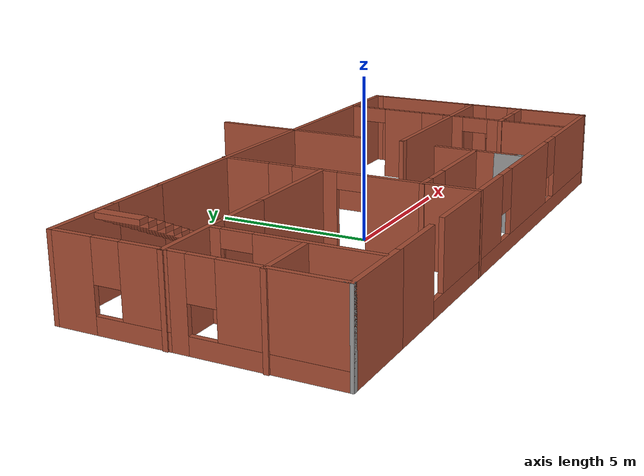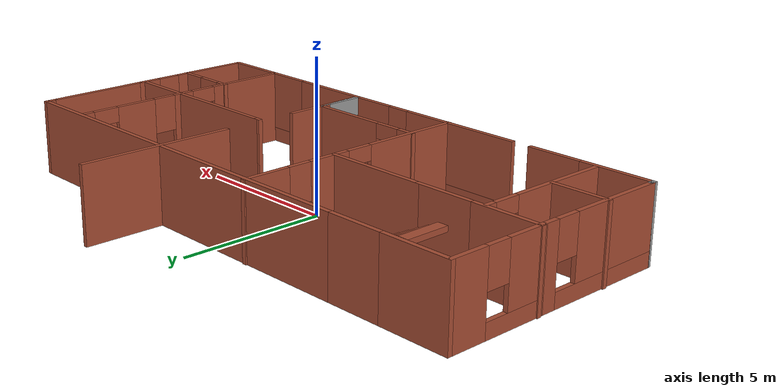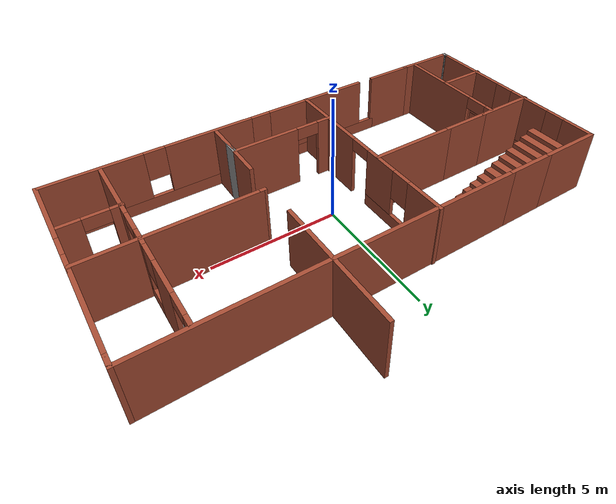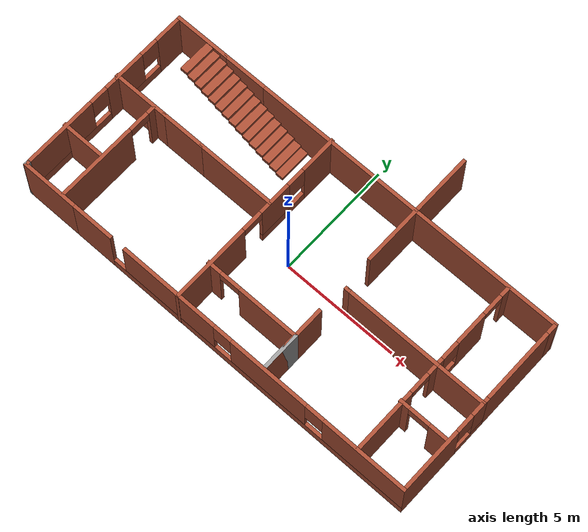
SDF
<?xml version='1.0'?>
<sdf version='1.7'>
  <model name='my_test_world'>
    <link name='Stairs_1'>
      <self_collide>0</self_collide>
      <enable_wind>0</enable_wind>
      <kinematic>0</kinematic>
      <pose>0 0 0 0 -0 0</pose>
      <visual name='Stairs_1_Visual_0'>
        <pose>-2.66061 3.11353 0.083333 0 -0 -1.5708</pose>
        <geometry>
          <box>
            <size>1.40227 0.336583 0.166667</size>
          </box>
        </geometry>
        <material>
          <script>
            <uri>file://media/materials/scripts/gazebo.material</uri>
            <name>Gazebo/Bricks</name>
          </script>
          <ambient>1 1 1 1</ambient>
          <shader type='pixel'/>
        </material>
        <meta>
          <layer>0</layer>
        </meta>
        <transparency>0</transparency>
        <cast_shadows>1</cast_shadows>
      </visual>
      <visual name='Stairs_1_Visual_1'>
        <pose>-2.99719 3.11353 0.25 0 -0 -1.5708</pose>
        <geometry>
          <box>
            <size>1.40227 0.336583 0.166667</size>
          </box>
        </geometry>
        <material>
          <script>
            <uri>file://media/materials/scripts/gazebo.material</uri>
            <name>Gazebo/Bricks</name>
          </script>
          <ambient>1 1 1 1</ambient>
          <shader type='pixel'/>
        </material>
        <meta>
          <layer>0</layer>
        </meta>
        <transparency>0</transparency>
        <cast_shadows>1</cast_shadows>
      </visual>
      <visual name='Stairs_1_Visual_2'>
        <pose>-3.33377 3.11353 0.416667 0 -0 -1.5708</pose>
        <geometry>
          <box>
            <size>1.40227 0.336583 0.166667</size>
          </box>
        </geometry>
        <material>
          <script>
            <uri>file://media/materials/scripts/gazebo.material</uri>
            <name>Gazebo/Bricks</name>
          </script>
          <ambient>1 1 1 1</ambient>
          <shader type='pixel'/>
        </material>
        <meta>
          <layer>0</layer>
        </meta>
        <transparency>0</transparency>
        <cast_shadows>1</cast_shadows>
      </visual>
      <visual name='Stairs_1_Visual_3'>
        <pose>-3.67036 3.11353 0.583333 0 -0 -1.5708</pose>
        <geometry>
          <box>
            <size>1.40227 0.336583 0.166667</size>
          </box>
        </geometry>
        <material>
          <script>
            <uri>file://media/materials/scripts/gazebo.material</uri>
            <name>Gazebo/Bricks</name>
          </script>
          <ambient>1 1 1 1</ambient>
          <shader type='pixel'/>
        </material>
        <meta>
          <layer>0</layer>
        </meta>
        <transparency>0</transparency>
        <cast_shadows>1</cast_shadows>
      </visual>
      <visual name='Stairs_1_Visual_4'>
        <pose>-4.00694 3.11353 0.75 0 -0 -1.5708</pose>
        <geometry>
          <box>
            <size>1.40227 0.336583 0.166667</size>
          </box>
        </geometry>
        <material>
          <script>
            <uri>file://media/materials/scripts/gazebo.material</uri>
            <name>Gazebo/Bricks</name>
          </script>
          <ambient>1 1 1 1</ambient>
          <shader type='pixel'/>
        </material>
        <meta>
          <layer>0</layer>
        </meta>
        <transparency>0</transparency>
        <cast_shadows>1</cast_shadows>
      </visual>
      <visual name='Stairs_1_Visual_8'>
        <pose>-5.35327 3.11353 1.41667 0 -0 -1.5708</pose>
        <geometry>
          <box>
            <size>1.40227 0.336583 0.166667</size>
          </box>
        </geometry>
        <material>
          <script>
            <uri>file://media/materials/scripts/gazebo.material</uri>
            <name>Gazebo/Bricks</name>
          </script>
          <ambient>1 1 1 1</ambient>
          <shader type='pixel'/>
        </material>
        <meta>
          <layer>0</layer>
        </meta>
        <transparency>0</transparency>
        <cast_shadows>1</cast_shadows>
      </visual>
      <visual name='Stairs_1_Visual_5'>
        <pose>-4.34352 3.11353 0.916667 0 -0 -1.5708</pose>
        <geometry>
          <box>
            <size>1.40227 0.336583 0.166667</size>
          </box>
        </geometry>
        <material>
          <script>
            <uri>file://media/materials/scripts/gazebo.material</uri>
            <name>Gazebo/Bricks</name>
          </script>
          <ambient>1 1 1 1</ambient>
          <shader type='pixel'/>
        </material>
        <meta>
          <layer>0</layer>
        </meta>
        <transparency>0</transparency>
        <cast_shadows>1</cast_shadows>
      </visual>
      <visual name='Stairs_1_Visual_6'>
        <pose>-4.68011 3.11353 1.08333 0 -0 -1.5708</pose>
        <geometry>
          <box>
            <size>1.40227 0.336583 0.166667</size>
          </box>
        </geometry>
        <material>
          <script>
            <uri>file://media/materials/scripts/gazebo.material</uri>
            <name>Gazebo/Bricks</name>
          </script>
          <ambient>1 1 1 1</ambient>
          <shader type='pixel'/>
        </material>
        <meta>
          <layer>0</layer>
        </meta>
        <transparency>0</transparency>
        <cast_shadows>1</cast_shadows>
      </visual>
      <visual name='Stairs_1_Visual_7'>
        <pose>-5.01669 3.11353 1.25 0 -0 -1.5708</pose>
        <geometry>
          <box>
            <size>1.40227 0.336583 0.166667</size>
          </box>
        </geometry>
        <material>
          <script>
            <uri>file://media/materials/scripts/gazebo.material</uri>
            <name>Gazebo/Bricks</name>
          </script>
          <ambient>1 1 1 1</ambient>
          <shader type='pixel'/>
        </material>
        <meta>
          <layer>0</layer>
        </meta>
        <transparency>0</transparency>
        <cast_shadows>1</cast_shadows>
      </visual>
      <visual name='Stairs_1_Visual_9'>
        <pose>-5.68986 3.11353 1.58333 0 -0 -1.5708</pose>
        <geometry>
          <box>
            <size>1.40227 0.336583 0.166667</size>
          </box>
        </geometry>
        <material>
          <script>
            <uri>file://media/materials/scripts/gazebo.material</uri>
            <name>Gazebo/Bricks</name>
          </script>
          <ambient>1 1 1 1</ambient>
          <shader type='pixel'/>
        </material>
        <meta>
          <layer>0</layer>
        </meta>
        <transparency>0</transparency>
        <cast_shadows>1</cast_shadows>
      </visual>
      <visual name='Stairs_1_Visual_10'>
        <pose>-6.02644 3.11353 1.75 0 -0 -1.5708</pose>
        <geometry>
          <box>
            <size>1.40227 0.336583 0.166667</size>
          </box>
        </geometry>
        <material>
          <script>
            <uri>file://media/materials/scripts/gazebo.material</uri>
            <name>Gazebo/Bricks</name>
          </script>
          <ambient>1 1 1 1</ambient>
          <shader type='pixel'/>
        </material>
        <meta>
          <layer>0</layer>
        </meta>
        <transparency>0</transparency>
        <cast_shadows>1</cast_shadows>
      </visual>
      <visual name='Stairs_1_Visual_11'>
        <pose>-6.36302 3.11353 1.91667 0 -0 -1.5708</pose>
        <geometry>
          <box>
            <size>1.40227 0.336583 0.166667</size>
          </box>
        </geometry>
        <material>
          <script>
            <uri>file://media/materials/scripts/gazebo.material</uri>
            <name>Gazebo/Bricks</name>
          </script>
          <ambient>1 1 1 1</ambient>
          <shader type='pixel'/>
        </material>
        <meta>
          <layer>0</layer>
        </meta>
        <transparency>0</transparency>
        <cast_shadows>1</cast_shadows>
      </visual>
      <visual name='Stairs_1_Visual_12'>
        <pose>-6.69961 3.11353 2.08333 0 -0 -1.5708</pose>
        <geometry>
          <box>
            <size>1.40227 0.336583 0.166667</size>
          </box>
        </geometry>
        <material>
          <script>
            <uri>file://media/materials/scripts/gazebo.material</uri>
            <name>Gazebo/Bricks</name>
          </script>
          <ambient>1 1 1 1</ambient>
          <shader type='pixel'/>
        </material>
        <meta>
          <layer>0</layer>
        </meta>
        <transparency>0</transparency>
        <cast_shadows>1</cast_shadows>
      </visual>
      <visual name='Stairs_1_Visual_13'>
        <pose>-7.03619 3.11353 2.25 0 -0 -1.5708</pose>
        <geometry>
          <box>
            <size>1.40227 0.336583 0.166667</size>
          </box>
        </geometry>
        <material>
          <script>
            <uri>file://media/materials/scripts/gazebo.material</uri>
            <name>Gazebo/Bricks</name>
          </script>
          <ambient>1 1 1 1</ambient>
          <shader type='pixel'/>
        </material>
        <meta>
          <layer>0</layer>
        </meta>
        <transparency>0</transparency>
        <cast_shadows>1</cast_shadows>
      </visual>
      <visual name='Stairs_1_Visual_14'>
        <pose>-7.37277 3.11353 2.41667 0 -0 -1.5708</pose>
        <geometry>
          <box>
            <size>1.40227 0.336583 0.166667</size>
          </box>
        </geometry>
        <material>
          <script>
            <uri>file://media/materials/scripts/gazebo.material</uri>
            <name>Gazebo/Bricks</name>
          </script>
          <ambient>1 1 1 1</ambient>
          <shader type='pixel'/>
        </material>
        <meta>
          <layer>0</layer>
        </meta>
        <transparency>0</transparency>
        <cast_shadows>1</cast_shadows>
      </visual>
      <collision name='Stairs_1_Collision_0'>
        <laser_retro>0</laser_retro>
        <max_contacts>10</max_contacts>
        <pose>-2.66061 3.11353 0.083333 0 0 -1.5708</pose>
        <geometry>
          <box>
            <size>1.40227 0.336583 0.166667</size>
          </box>
        </geometry>
        <surface>
          <friction>
            <ode>
              <mu>1</mu>
              <mu2>1</mu2>
              <fdir1>0 0 0</fdir1>
              <slip1>0</slip1>
              <slip2>0</slip2>
            </ode>
            <torsional>
              <coefficient>1</coefficient>
              <patch_radius>0</patch_radius>
              <surface_radius>0</surface_radius>
              <use_patch_radius>1</use_patch_radius>
              <ode>
                <slip>0</slip>
              </ode>
            </torsional>
          </friction>
          <bounce>
            <restitution_coefficient>0</restitution_coefficient>
            <threshold>1e+06</threshold>
          </bounce>
          <contact>
            <collide_without_contact>0</collide_without_contact>
            <collide_without_contact_bitmask>1</collide_without_contact_bitmask>
            <collide_bitmask>1</collide_bitmask>
            <ode>
              <soft_cfm>0</soft_cfm>
              <soft_erp>0.2</soft_erp>
              <kp>1e+13</kp>
              <kd>1</kd>
              <max_vel>0.01</max_vel>
              <min_depth>0</min_depth>
            </ode>
            <bullet>
              <split_impulse>1</split_impulse>
              <split_impulse_penetration_threshold>-0.01</split_impulse_penetration_threshold>
              <soft_cfm>0</soft_cfm>
              <soft_erp>0.2</soft_erp>
              <kp>1e+13</kp>
              <kd>1</kd>
            </bullet>
          </contact>
        </surface>
      </collision>
      <collision name='Stairs_1_Collision_1'>
        <laser_retro>0</laser_retro>
        <max_contacts>10</max_contacts>
        <pose>-2.99719 3.11353 0.25 0 0 -1.5708</pose>
        <geometry>
          <box>
            <size>1.40227 0.336583 0.166667</size>
          </box>
        </geometry>
        <surface>
          <friction>
            <ode>
              <mu>1</mu>
              <mu2>1</mu2>
              <fdir1>0 0 0</fdir1>
              <slip1>0</slip1>
              <slip2>0</slip2>
            </ode>
            <torsional>
              <coefficient>1</coefficient>
              <patch_radius>0</patch_radius>
              <surface_radius>0</surface_radius>
              <use_patch_radius>1</use_patch_radius>
              <ode>
                <slip>0</slip>
              </ode>
            </torsional>
          </friction>
          <bounce>
            <restitution_coefficient>0</restitution_coefficient>
            <threshold>1e+06</threshold>
          </bounce>
          <contact>
            <collide_without_contact>0</collide_without_contact>
            <collide_without_contact_bitmask>1</collide_without_contact_bitmask>
            <collide_bitmask>1</collide_bitmask>
            <ode>
              <soft_cfm>0</soft_cfm>
              <soft_erp>0.2</soft_erp>
              <kp>1e+13</kp>
              <kd>1</kd>
              <max_vel>0.01</max_vel>
              <min_depth>0</min_depth>
            </ode>
            <bullet>
              <split_impulse>1</split_impulse>
              <split_impulse_penetration_threshold>-0.01</split_impulse_penetration_threshold>
              <soft_cfm>0</soft_cfm>
              <soft_erp>0.2</soft_erp>
              <kp>1e+13</kp>
              <kd>1</kd>
            </bullet>
          </contact>
        </surface>
      </collision>
      <collision name='Stairs_1_Collision_2'>
        <laser_retro>0</laser_retro>
        <max_contacts>10</max_contacts>
        <pose>-3.33377 3.11353 0.416667 0 0 -1.5708</pose>
        <geometry>
          <box>
            <size>1.40227 0.336583 0.166667</size>
          </box>
        </geometry>
        <surface>
          <friction>
            <ode>
              <mu>1</mu>
              <mu2>1</mu2>
              <fdir1>0 0 0</fdir1>
              <slip1>0</slip1>
              <slip2>0</slip2>
            </ode>
            <torsional>
              <coefficient>1</coefficient>
              <patch_radius>0</patch_radius>
              <surface_radius>0</surface_radius>
              <use_patch_radius>1</use_patch_radius>
              <ode>
                <slip>0</slip>
              </ode>
            </torsional>
          </friction>
          <bounce>
            <restitution_coefficient>0</restitution_coefficient>
            <threshold>1e+06</threshold>
          </bounce>
          <contact>
            <collide_without_contact>0</collide_without_contact>
            <collide_without_contact_bitmask>1</collide_without_contact_bitmask>
            <collide_bitmask>1</collide_bitmask>
            <ode>
              <soft_cfm>0</soft_cfm>
              <soft_erp>0.2</soft_erp>
              <kp>1e+13</kp>
              <kd>1</kd>
              <max_vel>0.01</max_vel>
              <min_depth>0</min_depth>
            </ode>
            <bullet>
              <split_impulse>1</split_impulse>
              <split_impulse_penetration_threshold>-0.01</split_impulse_penetration_threshold>
              <soft_cfm>0</soft_cfm>
              <soft_erp>0.2</soft_erp>
              <kp>1e+13</kp>
              <kd>1</kd>
            </bullet>
          </contact>
        </surface>
      </collision>
      <collision name='Stairs_1_Collision_4'>
        <laser_retro>0</laser_retro>
        <max_contacts>10</max_contacts>
        <pose>-4.00694 3.11353 0.75 0 0 -1.5708</pose>
        <geometry>
          <box>
            <size>1.40227 0.336583 0.166667</size>
          </box>
        </geometry>
        <surface>
          <friction>
            <ode>
              <mu>1</mu>
              <mu2>1</mu2>
              <fdir1>0 0 0</fdir1>
              <slip1>0</slip1>
              <slip2>0</slip2>
            </ode>
            <torsional>
              <coefficient>1</coefficient>
              <patch_radius>0</patch_radius>
              <surface_radius>0</surface_radius>
              <use_patch_radius>1</use_patch_radius>
              <ode>
                <slip>0</slip>
              </ode>
            </torsional>
          </friction>
          <bounce>
            <restitution_coefficient>0</restitution_coefficient>
            <threshold>1e+06</threshold>
          </bounce>
          <contact>
            <collide_without_contact>0</collide_without_contact>
            <collide_without_contact_bitmask>1</collide_without_contact_bitmask>
            <collide_bitmask>1</collide_bitmask>
            <ode>
              <soft_cfm>0</soft_cfm>
              <soft_erp>0.2</soft_erp>
              <kp>1e+13</kp>
              <kd>1</kd>
              <max_vel>0.01</max_vel>
              <min_depth>0</min_depth>
            </ode>
            <bullet>
              <split_impulse>1</split_impulse>
              <split_impulse_penetration_threshold>-0.01</split_impulse_penetration_threshold>
              <soft_cfm>0</soft_cfm>
              <soft_erp>0.2</soft_erp>
              <kp>1e+13</kp>
              <kd>1</kd>
            </bullet>
          </contact>
        </surface>
      </collision>
      <collision name='Stairs_1_Collision_3'>
        <laser_retro>0</laser_retro>
        <max_contacts>10</max_contacts>
        <pose>-3.67036 3.11353 0.583333 0 0 -1.5708</pose>
        <geometry>
          <box>
            <size>1.40227 0.336583 0.166667</size>
          </box>
        </geometry>
        <surface>
          <friction>
            <ode>
              <mu>1</mu>
              <mu2>1</mu2>
              <fdir1>0 0 0</fdir1>
              <slip1>0</slip1>
              <slip2>0</slip2>
            </ode>
            <torsional>
              <coefficient>1</coefficient>
              <patch_radius>0</patch_radius>
              <surface_radius>0</surface_radius>
              <use_patch_radius>1</use_patch_radius>
              <ode>
                <slip>0</slip>
              </ode>
            </torsional>
          </friction>
          <bounce>
            <restitution_coefficient>0</restitution_coefficient>
            <threshold>1e+06</threshold>
          </bounce>
          <contact>
            <collide_without_contact>0</collide_without_contact>
            <collide_without_contact_bitmask>1</collide_without_contact_bitmask>
            <collide_bitmask>1</collide_bitmask>
            <ode>
              <soft_cfm>0</soft_cfm>
              <soft_erp>0.2</soft_erp>
              <kp>1e+13</kp>
              <kd>1</kd>
              <max_vel>0.01</max_vel>
              <min_depth>0</min_depth>
            </ode>
            <bullet>
              <split_impulse>1</split_impulse>
              <split_impulse_penetration_threshold>-0.01</split_impulse_penetration_threshold>
              <soft_cfm>0</soft_cfm>
              <soft_erp>0.2</soft_erp>
              <kp>1e+13</kp>
              <kd>1</kd>
            </bullet>
          </contact>
        </surface>
      </collision>
      <collision name='Stairs_1_Collision_5'>
        <laser_retro>0</laser_retro>
        <max_contacts>10</max_contacts>
        <pose>-4.34352 3.11353 0.916667 0 0 -1.5708</pose>
        <geometry>
          <box>
            <size>1.40227 0.336583 0.166667</size>
          </box>
        </geometry>
        <surface>
          <friction>
            <ode>
              <mu>1</mu>
              <mu2>1</mu2>
              <fdir1>0 0 0</fdir1>
              <slip1>0</slip1>
              <slip2>0</slip2>
            </ode>
            <torsional>
              <coefficient>1</coefficient>
              <patch_radius>0</patch_radius>
              <surface_radius>0</surface_radius>
              <use_patch_radius>1</use_patch_radius>
              <ode>
                <slip>0</slip>
              </ode>
            </torsional>
          </friction>
          <bounce>
            <restitution_coefficient>0</restitution_coefficient>
            <threshold>1e+06</threshold>
          </bounce>
          <contact>
            <collide_without_contact>0</collide_without_contact>
            <collide_without_contact_bitmask>1</collide_without_contact_bitmask>
            <collide_bitmask>1</collide_bitmask>
            <ode>
              <soft_cfm>0</soft_cfm>
              <soft_erp>0.2</soft_erp>
              <kp>1e+13</kp>
              <kd>1</kd>
              <max_vel>0.01</max_vel>
              <min_depth>0</min_depth>
            </ode>
            <bullet>
              <split_impulse>1</split_impulse>
              <split_impulse_penetration_threshold>-0.01</split_impulse_penetration_threshold>
              <soft_cfm>0</soft_cfm>
              <soft_erp>0.2</soft_erp>
              <kp>1e+13</kp>
              <kd>1</kd>
            </bullet>
          </contact>
        </surface>
      </collision>
      <collision name='Stairs_1_Collision_6'>
        <laser_retro>0</laser_retro>
        <max_contacts>10</max_contacts>
        <pose>-4.68011 3.11353 1.08333 0 0 -1.5708</pose>
        <geometry>
          <box>
            <size>1.40227 0.336583 0.166667</size>
          </box>
        </geometry>
        <surface>
          <friction>
            <ode>
              <mu>1</mu>
              <mu2>1</mu2>
              <fdir1>0 0 0</fdir1>
              <slip1>0</slip1>
              <slip2>0</slip2>
            </ode>
            <torsional>
              <coefficient>1</coefficient>
              <patch_radius>0</patch_radius>
              <surface_radius>0</surface_radius>
              <use_patch_radius>1</use_patch_radius>
              <ode>
                <slip>0</slip>
              </ode>
            </torsional>
          </friction>
          <bounce>
            <restitution_coefficient>0</restitution_coefficient>
            <threshold>1e+06</threshold>
          </bounce>
          <contact>
            <collide_without_contact>0</collide_without_contact>
            <collide_without_contact_bitmask>1</collide_without_contact_bitmask>
            <collide_bitmask>1</collide_bitmask>
            <ode>
              <soft_cfm>0</soft_cfm>
              <soft_erp>0.2</soft_erp>
              <kp>1e+13</kp>
              <kd>1</kd>
              <max_vel>0.01</max_vel>
              <min_depth>0</min_depth>
            </ode>
            <bullet>
              <split_impulse>1</split_impulse>
              <split_impulse_penetration_threshold>-0.01</split_impulse_penetration_threshold>
              <soft_cfm>0</soft_cfm>
              <soft_erp>0.2</soft_erp>
              <kp>1e+13</kp>
              <kd>1</kd>
            </bullet>
          </contact>
        </surface>
      </collision>
      <collision name='Stairs_1_Collision_7'>
        <laser_retro>0</laser_retro>
        <max_contacts>10</max_contacts>
        <pose>-5.01669 3.11353 1.25 0 0 -1.5708</pose>
        <geometry>
          <box>
            <size>1.40227 0.336583 0.166667</size>
          </box>
        </geometry>
        <surface>
          <friction>
            <ode>
              <mu>1</mu>
              <mu2>1</mu2>
              <fdir1>0 0 0</fdir1>
              <slip1>0</slip1>
              <slip2>0</slip2>
            </ode>
            <torsional>
              <coefficient>1</coefficient>
              <patch_radius>0</patch_radius>
              <surface_radius>0</surface_radius>
              <use_patch_radius>1</use_patch_radius>
              <ode>
                <slip>0</slip>
              </ode>
            </torsional>
          </friction>
          <bounce>
            <restitution_coefficient>0</restitution_coefficient>
            <threshold>1e+06</threshold>
          </bounce>
          <contact>
            <collide_without_contact>0</collide_without_contact>
            <collide_without_contact_bitmask>1</collide_without_contact_bitmask>
            <collide_bitmask>1</collide_bitmask>
            <ode>
              <soft_cfm>0</soft_cfm>
              <soft_erp>0.2</soft_erp>
              <kp>1e+13</kp>
              <kd>1</kd>
              <max_vel>0.01</max_vel>
              <min_depth>0</min_depth>
            </ode>
            <bullet>
              <split_impulse>1</split_impulse>
              <split_impulse_penetration_threshold>-0.01</split_impulse_penetration_threshold>
              <soft_cfm>0</soft_cfm>
              <soft_erp>0.2</soft_erp>
              <kp>1e+13</kp>
              <kd>1</kd>
            </bullet>
          </contact>
        </surface>
      </collision>
      <collision name='Stairs_1_Collision_8'>
        <laser_retro>0</laser_retro>
        <max_contacts>10</max_contacts>
        <pose>-5.35327 3.11353 1.41667 0 0 -1.5708</pose>
        <geometry>
          <box>
            <size>1.40227 0.336583 0.166667</size>
          </box>
        </geometry>
        <surface>
          <friction>
            <ode>
              <mu>1</mu>
              <mu2>1</mu2>
              <fdir1>0 0 0</fdir1>
              <slip1>0</slip1>
              <slip2>0</slip2>
            </ode>
            <torsional>
              <coefficient>1</coefficient>
              <patch_radius>0</patch_radius>
              <surface_radius>0</surface_radius>
              <use_patch_radius>1</use_patch_radius>
              <ode>
                <slip>0</slip>
              </ode>
            </torsional>
          </friction>
          <bounce>
            <restitution_coefficient>0</restitution_coefficient>
            <threshold>1e+06</threshold>
          </bounce>
          <contact>
            <collide_without_contact>0</collide_without_contact>
            <collide_without_contact_bitmask>1</collide_without_contact_bitmask>
            <collide_bitmask>1</collide_bitmask>
            <ode>
              <soft_cfm>0</soft_cfm>
              <soft_erp>0.2</soft_erp>
              <kp>1e+13</kp>
              <kd>1</kd>
              <max_vel>0.01</max_vel>
              <min_depth>0</min_depth>
            </ode>
            <bullet>
              <split_impulse>1</split_impulse>
              <split_impulse_penetration_threshold>-0.01</split_impulse_penetration_threshold>
              <soft_cfm>0</soft_cfm>
              <soft_erp>0.2</soft_erp>
              <kp>1e+13</kp>
              <kd>1</kd>
            </bullet>
          </contact>
        </surface>
      </collision>
      <collision name='Stairs_1_Collision_9'>
        <laser_retro>0</laser_retro>
        <max_contacts>10</max_contacts>
        <pose>-5.68986 3.11353 1.58333 0 0 -1.5708</pose>
        <geometry>
          <box>
            <size>1.40227 0.336583 0.166667</size>
          </box>
        </geometry>
        <surface>
          <friction>
            <ode>
              <mu>1</mu>
              <mu2>1</mu2>
              <fdir1>0 0 0</fdir1>
              <slip1>0</slip1>
              <slip2>0</slip2>
            </ode>
            <torsional>
              <coefficient>1</coefficient>
              <patch_radius>0</patch_radius>
              <surface_radius>0</surface_radius>
              <use_patch_radius>1</use_patch_radius>
              <ode>
                <slip>0</slip>
              </ode>
            </torsional>
          </friction>
          <bounce>
            <restitution_coefficient>0</restitution_coefficient>
            <threshold>1e+06</threshold>
          </bounce>
          <contact>
            <collide_without_contact>0</collide_without_contact>
            <collide_without_contact_bitmask>1</collide_without_contact_bitmask>
            <collide_bitmask>1</collide_bitmask>
            <ode>
              <soft_cfm>0</soft_cfm>
              <soft_erp>0.2</soft_erp>
              <kp>1e+13</kp>
              <kd>1</kd>
              <max_vel>0.01</max_vel>
              <min_depth>0</min_depth>
            </ode>
            <bullet>
              <split_impulse>1</split_impulse>
              <split_impulse_penetration_threshold>-0.01</split_impulse_penetration_threshold>
              <soft_cfm>0</soft_cfm>
              <soft_erp>0.2</soft_erp>
              <kp>1e+13</kp>
              <kd>1</kd>
            </bullet>
          </contact>
        </surface>
      </collision>
      <collision name='Stairs_1_Collision_10'>
        <laser_retro>0</laser_retro>
        <max_contacts>10</max_contacts>
        <pose>-6.02644 3.11353 1.75 0 0 -1.5708</pose>
        <geometry>
          <box>
            <size>1.40227 0.336583 0.166667</size>
          </box>
        </geometry>
        <surface>
          <friction>
            <ode>
              <mu>1</mu>
              <mu2>1</mu2>
              <fdir1>0 0 0</fdir1>
              <slip1>0</slip1>
              <slip2>0</slip2>
            </ode>
            <torsional>
              <coefficient>1</coefficient>
              <patch_radius>0</patch_radius>
              <surface_radius>0</surface_radius>
              <use_patch_radius>1</use_patch_radius>
              <ode>
                <slip>0</slip>
              </ode>
            </torsional>
          </friction>
          <bounce>
            <restitution_coefficient>0</restitution_coefficient>
            <threshold>1e+06</threshold>
          </bounce>
          <contact>
            <collide_without_contact>0</collide_without_contact>
            <collide_without_contact_bitmask>1</collide_without_contact_bitmask>
            <collide_bitmask>1</collide_bitmask>
            <ode>
              <soft_cfm>0</soft_cfm>
              <soft_erp>0.2</soft_erp>
              <kp>1e+13</kp>
              <kd>1</kd>
              <max_vel>0.01</max_vel>
              <min_depth>0</min_depth>
            </ode>
            <bullet>
              <split_impulse>1</split_impulse>
              <split_impulse_penetration_threshold>-0.01</split_impulse_penetration_threshold>
              <soft_cfm>0</soft_cfm>
              <soft_erp>0.2</soft_erp>
              <kp>1e+13</kp>
              <kd>1</kd>
            </bullet>
          </contact>
        </surface>
      </collision>
      <collision name='Stairs_1_Collision_11'>
        <laser_retro>0</laser_retro>
        <max_contacts>10</max_contacts>
        <pose>-6.36302 3.11353 1.91667 0 0 -1.5708</pose>
        <geometry>
          <box>
            <size>1.40227 0.336583 0.166667</size>
          </box>
        </geometry>
        <surface>
          <friction>
            <ode>
              <mu>1</mu>
              <mu2>1</mu2>
              <fdir1>0 0 0</fdir1>
              <slip1>0</slip1>
              <slip2>0</slip2>
            </ode>
            <torsional>
              <coefficient>1</coefficient>
              <patch_radius>0</patch_radius>
              <surface_radius>0</surface_radius>
              <use_patch_radius>1</use_patch_radius>
              <ode>
                <slip>0</slip>
              </ode>
            </torsional>
          </friction>
          <bounce>
            <restitution_coefficient>0</restitution_coefficient>
            <threshold>1e+06</threshold>
          </bounce>
          <contact>
            <collide_without_contact>0</collide_without_contact>
            <collide_without_contact_bitmask>1</collide_without_contact_bitmask>
            <collide_bitmask>1</collide_bitmask>
            <ode>
              <soft_cfm>0</soft_cfm>
              <soft_erp>0.2</soft_erp>
              <kp>1e+13</kp>
              <kd>1</kd>
              <max_vel>0.01</max_vel>
              <min_depth>0</min_depth>
            </ode>
            <bullet>
              <split_impulse>1</split_impulse>
              <split_impulse_penetration_threshold>-0.01</split_impulse_penetration_threshold>
              <soft_cfm>0</soft_cfm>
              <soft_erp>0.2</soft_erp>
              <kp>1e+13</kp>
              <kd>1</kd>
            </bullet>
          </contact>
        </surface>
      </collision>
      <collision name='Stairs_1_Collision_12'>
        <laser_retro>0</laser_retro>
        <max_contacts>10</max_contacts>
        <pose>-6.69961 3.11353 2.08333 0 0 -1.5708</pose>
        <geometry>
          <box>
            <size>1.40227 0.336583 0.166667</size>
          </box>
        </geometry>
        <surface>
          <friction>
            <ode>
              <mu>1</mu>
              <mu2>1</mu2>
              <fdir1>0 0 0</fdir1>
              <slip1>0</slip1>
              <slip2>0</slip2>
            </ode>
            <torsional>
              <coefficient>1</coefficient>
              <patch_radius>0</patch_radius>
              <surface_radius>0</surface_radius>
              <use_patch_radius>1</use_patch_radius>
              <ode>
                <slip>0</slip>
              </ode>
            </torsional>
          </friction>
          <bounce>
            <restitution_coefficient>0</restitution_coefficient>
            <threshold>1e+06</threshold>
          </bounce>
          <contact>
            <collide_without_contact>0</collide_without_contact>
            <collide_without_contact_bitmask>1</collide_without_contact_bitmask>
            <collide_bitmask>1</collide_bitmask>
            <ode>
              <soft_cfm>0</soft_cfm>
              <soft_erp>0.2</soft_erp>
              <kp>1e+13</kp>
              <kd>1</kd>
              <max_vel>0.01</max_vel>
              <min_depth>0</min_depth>
            </ode>
            <bullet>
              <split_impulse>1</split_impulse>
              <split_impulse_penetration_threshold>-0.01</split_impulse_penetration_threshold>
              <soft_cfm>0</soft_cfm>
              <soft_erp>0.2</soft_erp>
              <kp>1e+13</kp>
              <kd>1</kd>
            </bullet>
          </contact>
        </surface>
      </collision>
      <collision name='Stairs_1_Collision_13'>
        <laser_retro>0</laser_retro>
        <max_contacts>10</max_contacts>
        <pose>-7.03619 3.11353 2.25 0 0 -1.5708</pose>
        <geometry>
          <box>
            <size>1.40227 0.336583 0.166667</size>
          </box>
        </geometry>
        <surface>
          <friction>
            <ode>
              <mu>1</mu>
              <mu2>1</mu2>
              <fdir1>0 0 0</fdir1>
              <slip1>0</slip1>
              <slip2>0</slip2>
            </ode>
            <torsional>
              <coefficient>1</coefficient>
              <patch_radius>0</patch_radius>
              <surface_radius>0</surface_radius>
              <use_patch_radius>1</use_patch_radius>
              <ode>
                <slip>0</slip>
              </ode>
            </torsional>
          </friction>
          <bounce>
            <restitution_coefficient>0</restitution_coefficient>
            <threshold>1e+06</threshold>
          </bounce>
          <contact>
            <collide_without_contact>0</collide_without_contact>
            <collide_without_contact_bitmask>1</collide_without_contact_bitmask>
            <collide_bitmask>1</collide_bitmask>
            <ode>
              <soft_cfm>0</soft_cfm>
              <soft_erp>0.2</soft_erp>
              <kp>1e+13</kp>
              <kd>1</kd>
              <max_vel>0.01</max_vel>
              <min_depth>0</min_depth>
            </ode>
            <bullet>
              <split_impulse>1</split_impulse>
              <split_impulse_penetration_threshold>-0.01</split_impulse_penetration_threshold>
              <soft_cfm>0</soft_cfm>
              <soft_erp>0.2</soft_erp>
              <kp>1e+13</kp>
              <kd>1</kd>
            </bullet>
          </contact>
        </surface>
      </collision>
      <collision name='Stairs_1_Collision_14'>
        <laser_retro>0</laser_retro>
        <max_contacts>10</max_contacts>
        <pose>-7.37277 3.11353 2.41667 0 0 -1.5708</pose>
        <geometry>
          <box>
            <size>1.40227 0.336583 0.166667</size>
          </box>
        </geometry>
        <surface>
          <friction>
            <ode>
              <mu>1</mu>
              <mu2>1</mu2>
              <fdir1>0 0 0</fdir1>
              <slip1>0</slip1>
              <slip2>0</slip2>
            </ode>
            <torsional>
              <coefficient>1</coefficient>
              <patch_radius>0</patch_radius>
              <surface_radius>0</surface_radius>
              <use_patch_radius>1</use_patch_radius>
              <ode>
                <slip>0</slip>
              </ode>
            </torsional>
          </friction>
          <bounce>
            <restitution_coefficient>0</restitution_coefficient>
            <threshold>1e+06</threshold>
          </bounce>
          <contact>
            <collide_without_contact>0</collide_without_contact>
            <collide_without_contact_bitmask>1</collide_without_contact_bitmask>
            <collide_bitmask>1</collide_bitmask>
            <ode>
              <soft_cfm>0</soft_cfm>
              <soft_erp>0.2</soft_erp>
              <kp>1e+13</kp>
              <kd>1</kd>
              <max_vel>0.01</max_vel>
              <min_depth>0</min_depth>
            </ode>
            <bullet>
              <split_impulse>1</split_impulse>
              <split_impulse_penetration_threshold>-0.01</split_impulse_penetration_threshold>
              <soft_cfm>0</soft_cfm>
              <soft_erp>0.2</soft_erp>
              <kp>1e+13</kp>
              <kd>1</kd>
            </bullet>
          </contact>
        </surface>
      </collision>
    </link>
    <link name='Wall_12'>
      <pose>2.12401 -4.15318 0 0 -0 0</pose>
      <self_collide>0</self_collide>
      <enable_wind>0</enable_wind>
      <kinematic>0</kinematic>
      <visual name='Wall_12_Visual_0'>
        <pose>0 0 0.25 0 -0 0</pose>
        <geometry>
          <box>
            <size>14 0.15 0.5</size>
          </box>
        </geometry>
        <material>
          <script>
            <uri>file://media/materials/scripts/gazebo.material</uri>
            <name>Gazebo/Bricks</name>
          </script>
          <ambient>1 1 1 1</ambient>
          <shader type='pixel'/>
        </material>
        <meta>
          <layer>0</layer>
        </meta>
        <transparency>0</transparency>
        <cast_shadows>1</cast_shadows>
      </visual>
      <visual name='Wall_12_Visual_1'>
        <pose>-4.05327 0 1.5 0 -0 0</pose>
        <geometry>
          <box>
            <size>4.3893 0.15 2</size>
          </box>
        </geometry>
        <material>
          <script>
            <uri>file://media/materials/scripts/gazebo.material</uri>
            <name>Gazebo/Bricks</name>
          </script>
          <ambient>1 1 1 1</ambient>
          <shader type='pixel'/>
        </material>
        <meta>
          <layer>0</layer>
        </meta>
        <transparency>0</transparency>
        <cast_shadows>1</cast_shadows>
      </visual>
      <visual name='Wall_12_Visual_2'>
        <pose>0.703592 0 1.5 0 -0 0</pose>
        <geometry>
          <box>
            <size>3.52442 0.15 2</size>
          </box>
        </geometry>
        <material>
          <script>
            <uri>file://media/materials/scripts/gazebo.material</uri>
            <name>Gazebo/Bricks</name>
          </script>
          <ambient>1 1 1 1</ambient>
          <shader type='pixel'/>
        </material>
        <meta>
          <layer>0</layer>
        </meta>
        <transparency>0</transparency>
        <cast_shadows>1</cast_shadows>
      </visual>
      <visual name='Wall_12_Visual_3'>
        <pose>5.1329 0 1.5 0 -0 0</pose>
        <geometry>
          <box>
            <size>3.7342 0.15 2</size>
          </box>
        </geometry>
        <material>
          <script>
            <uri>file://media/materials/scripts/gazebo.material</uri>
            <name>Gazebo/Bricks</name>
          </script>
          <ambient>1 1 1 1</ambient>
          <shader type='pixel'/>
        </material>
        <meta>
          <layer>0</layer>
        </meta>
        <transparency>0</transparency>
        <cast_shadows>1</cast_shadows>
      </visual>
      <visual name='Wall_12_Visual_4'>
        <pose>-1.45862 0 1.9 0 -0 0</pose>
        <geometry>
          <box>
            <size>0.8 0.15 1.2</size>
          </box>
        </geometry>
        <material>
          <script>
            <uri>file://media/materials/scripts/gazebo.material</uri>
            <name>Gazebo/Bricks</name>
          </script>
          <ambient>1 1 1 1</ambient>
          <shader type='pixel'/>
        </material>
        <meta>
          <layer>0</layer>
        </meta>
        <transparency>0</transparency>
        <cast_shadows>1</cast_shadows>
      </visual>
      <visual name='Wall_12_Visual_5'>
        <pose>2.8658 0 1.9 0 -0 0</pose>
        <geometry>
          <box>
            <size>0.8 0.15 1.2</size>
          </box>
        </geometry>
        <material>
          <script>
            <uri>file://media/materials/scripts/gazebo.material</uri>
            <name>Gazebo/Bricks</name>
          </script>
          <ambient>1 1 1 1</ambient>
          <shader type='pixel'/>
        </material>
        <meta>
          <layer>0</layer>
        </meta>
        <transparency>0</transparency>
        <cast_shadows>1</cast_shadows>
      </visual>
      <collision name='Wall_12_Collision_0'>
        <laser_retro>0</laser_retro>
        <max_contacts>10</max_contacts>
        <pose>0 0 0.25 0 -0 0</pose>
        <geometry>
          <box>
            <size>14 0.15 0.5</size>
          </box>
        </geometry>
        <surface>
          <friction>
            <ode>
              <mu>1</mu>
              <mu2>1</mu2>
              <fdir1>0 0 0</fdir1>
              <slip1>0</slip1>
              <slip2>0</slip2>
            </ode>
            <torsional>
              <coefficient>1</coefficient>
              <patch_radius>0</patch_radius>
              <surface_radius>0</surface_radius>
              <use_patch_radius>1</use_patch_radius>
              <ode>
                <slip>0</slip>
              </ode>
            </torsional>
          </friction>
          <bounce>
            <restitution_coefficient>0</restitution_coefficient>
            <threshold>1e+06</threshold>
          </bounce>
          <contact>
            <collide_without_contact>0</collide_without_contact>
            <collide_without_contact_bitmask>1</collide_without_contact_bitmask>
            <collide_bitmask>1</collide_bitmask>
            <ode>
              <soft_cfm>0</soft_cfm>
              <soft_erp>0.2</soft_erp>
              <kp>1e+13</kp>
              <kd>1</kd>
              <max_vel>0.01</max_vel>
              <min_depth>0</min_depth>
            </ode>
            <bullet>
              <split_impulse>1</split_impulse>
              <split_impulse_penetration_threshold>-0.01</split_impulse_penetration_threshold>
              <soft_cfm>0</soft_cfm>
              <soft_erp>0.2</soft_erp>
              <kp>1e+13</kp>
              <kd>1</kd>
            </bullet>
          </contact>
        </surface>
      </collision>
      <collision name='Wall_12_Collision_1'>
        <laser_retro>0</laser_retro>
        <max_contacts>10</max_contacts>
        <pose>-4.05327 0 1.5 0 -0 0</pose>
        <geometry>
          <box>
            <size>4.3893 0.15 2</size>
          </box>
        </geometry>
        <surface>
          <friction>
            <ode>
              <mu>1</mu>
              <mu2>1</mu2>
              <fdir1>0 0 0</fdir1>
              <slip1>0</slip1>
              <slip2>0</slip2>
            </ode>
            <torsional>
              <coefficient>1</coefficient>
              <patch_radius>0</patch_radius>
              <surface_radius>0</surface_radius>
              <use_patch_radius>1</use_patch_radius>
              <ode>
                <slip>0</slip>
              </ode>
            </torsional>
          </friction>
          <bounce>
            <restitution_coefficient>0</restitution_coefficient>
            <threshold>1e+06</threshold>
          </bounce>
          <contact>
            <collide_without_contact>0</collide_without_contact>
            <collide_without_contact_bitmask>1</collide_without_contact_bitmask>
            <collide_bitmask>1</collide_bitmask>
            <ode>
              <soft_cfm>0</soft_cfm>
              <soft_erp>0.2</soft_erp>
              <kp>1e+13</kp>
              <kd>1</kd>
              <max_vel>0.01</max_vel>
              <min_depth>0</min_depth>
            </ode>
            <bullet>
              <split_impulse>1</split_impulse>
              <split_impulse_penetration_threshold>-0.01</split_impulse_penetration_threshold>
              <soft_cfm>0</soft_cfm>
              <soft_erp>0.2</soft_erp>
              <kp>1e+13</kp>
              <kd>1</kd>
            </bullet>
          </contact>
        </surface>
      </collision>
      <collision name='Wall_12_Collision_2'>
        <laser_retro>0</laser_retro>
        <max_contacts>10</max_contacts>
        <pose>0.703592 0 1.5 0 -0 0</pose>
        <geometry>
          <box>
            <size>3.52442 0.15 2</size>
          </box>
        </geometry>
        <surface>
          <friction>
            <ode>
              <mu>1</mu>
              <mu2>1</mu2>
              <fdir1>0 0 0</fdir1>
              <slip1>0</slip1>
              <slip2>0</slip2>
            </ode>
            <torsional>
              <coefficient>1</coefficient>
              <patch_radius>0</patch_radius>
              <surface_radius>0</surface_radius>
              <use_patch_radius>1</use_patch_radius>
              <ode>
                <slip>0</slip>
              </ode>
            </torsional>
          </friction>
          <bounce>
            <restitution_coefficient>0</restitution_coefficient>
            <threshold>1e+06</threshold>
          </bounce>
          <contact>
            <collide_without_contact>0</collide_without_contact>
            <collide_without_contact_bitmask>1</collide_without_contact_bitmask>
            <collide_bitmask>1</collide_bitmask>
            <ode>
              <soft_cfm>0</soft_cfm>
              <soft_erp>0.2</soft_erp>
              <kp>1e+13</kp>
              <kd>1</kd>
              <max_vel>0.01</max_vel>
              <min_depth>0</min_depth>
            </ode>
            <bullet>
              <split_impulse>1</split_impulse>
              <split_impulse_penetration_threshold>-0.01</split_impulse_penetration_threshold>
              <soft_cfm>0</soft_cfm>
              <soft_erp>0.2</soft_erp>
              <kp>1e+13</kp>
              <kd>1</kd>
            </bullet>
          </contact>
        </surface>
      </collision>
      <collision name='Wall_12_Collision_3'>
        <laser_retro>0</laser_retro>
        <max_contacts>10</max_contacts>
        <pose>5.1329 0 1.5 0 -0 0</pose>
        <geometry>
          <box>
            <size>3.7342 0.15 2</size>
          </box>
        </geometry>
        <surface>
          <friction>
            <ode>
              <mu>1</mu>
              <mu2>1</mu2>
              <fdir1>0 0 0</fdir1>
              <slip1>0</slip1>
              <slip2>0</slip2>
            </ode>
            <torsional>
              <coefficient>1</coefficient>
              <patch_radius>0</patch_radius>
              <surface_radius>0</surface_radius>
              <use_patch_radius>1</use_patch_radius>
              <ode>
                <slip>0</slip>
              </ode>
            </torsional>
          </friction>
          <bounce>
            <restitution_coefficient>0</restitution_coefficient>
            <threshold>1e+06</threshold>
          </bounce>
          <contact>
            <collide_without_contact>0</collide_without_contact>
            <collide_without_contact_bitmask>1</collide_without_contact_bitmask>
            <collide_bitmask>1</collide_bitmask>
            <ode>
              <soft_cfm>0</soft_cfm>
              <soft_erp>0.2</soft_erp>
              <kp>1e+13</kp>
              <kd>1</kd>
              <max_vel>0.01</max_vel>
              <min_depth>0</min_depth>
            </ode>
            <bullet>
              <split_impulse>1</split_impulse>
              <split_impulse_penetration_threshold>-0.01</split_impulse_penetration_threshold>
              <soft_cfm>0</soft_cfm>
              <soft_erp>0.2</soft_erp>
              <kp>1e+13</kp>
              <kd>1</kd>
            </bullet>
          </contact>
        </surface>
      </collision>
      <collision name='Wall_12_Collision_5'>
        <laser_retro>0</laser_retro>
        <max_contacts>10</max_contacts>
        <pose>2.8658 0 1.9 0 -0 0</pose>
        <geometry>
          <box>
            <size>0.8 0.15 1.2</size>
          </box>
        </geometry>
        <surface>
          <friction>
            <ode>
              <mu>1</mu>
              <mu2>1</mu2>
              <fdir1>0 0 0</fdir1>
              <slip1>0</slip1>
              <slip2>0</slip2>
            </ode>
            <torsional>
              <coefficient>1</coefficient>
              <patch_radius>0</patch_radius>
              <surface_radius>0</surface_radius>
              <use_patch_radius>1</use_patch_radius>
              <ode>
                <slip>0</slip>
              </ode>
            </torsional>
          </friction>
          <bounce>
            <restitution_coefficient>0</restitution_coefficient>
            <threshold>1e+06</threshold>
          </bounce>
          <contact>
            <collide_without_contact>0</collide_without_contact>
            <collide_without_contact_bitmask>1</collide_without_contact_bitmask>
            <collide_bitmask>1</collide_bitmask>
            <ode>
              <soft_cfm>0</soft_cfm>
              <soft_erp>0.2</soft_erp>
              <kp>1e+13</kp>
              <kd>1</kd>
              <max_vel>0.01</max_vel>
              <min_depth>0</min_depth>
            </ode>
            <bullet>
              <split_impulse>1</split_impulse>
              <split_impulse_penetration_threshold>-0.01</split_impulse_penetration_threshold>
              <soft_cfm>0</soft_cfm>
              <soft_erp>0.2</soft_erp>
              <kp>1e+13</kp>
              <kd>1</kd>
            </bullet>
          </contact>
        </surface>
      </collision>
      <collision name='Wall_12_Collision_4'>
        <laser_retro>0</laser_retro>
        <max_contacts>10</max_contacts>
        <pose>-1.45862 0 1.9 0 -0 0</pose>
        <geometry>
          <box>
            <size>0.8 0.15 1.2</size>
          </box>
        </geometry>
        <surface>
          <friction>
            <ode>
              <mu>1</mu>
              <mu2>1</mu2>
              <fdir1>0 0 0</fdir1>
              <slip1>0</slip1>
              <slip2>0</slip2>
            </ode>
            <torsional>
              <coefficient>1</coefficient>
              <patch_radius>0</patch_radius>
              <surface_radius>0</surface_radius>
              <use_patch_radius>1</use_patch_radius>
              <ode>
                <slip>0</slip>
              </ode>
            </torsional>
          </friction>
          <bounce>
            <restitution_coefficient>0</restitution_coefficient>
            <threshold>1e+06</threshold>
          </bounce>
          <contact>
            <collide_without_contact>0</collide_without_contact>
            <collide_without_contact_bitmask>1</collide_without_contact_bitmask>
            <collide_bitmask>1</collide_bitmask>
            <ode>
              <soft_cfm>0</soft_cfm>
              <soft_erp>0.2</soft_erp>
              <kp>1e+13</kp>
              <kd>1</kd>
              <max_vel>0.01</max_vel>
              <min_depth>0</min_depth>
            </ode>
            <bullet>
              <split_impulse>1</split_impulse>
              <split_impulse_penetration_threshold>-0.01</split_impulse_penetration_threshold>
              <soft_cfm>0</soft_cfm>
              <soft_erp>0.2</soft_erp>
              <kp>1e+13</kp>
              <kd>1</kd>
            </bullet>
          </contact>
        </surface>
      </collision>
    </link>
    <link name='Wall_13'>
      <pose>9.04901 -1.97818 0 0 -0 1.5708</pose>
      <self_collide>0</self_collide>
      <enable_wind>0</enable_wind>
      <kinematic>0</kinematic>
      <visual name='Wall_13_Visual_0'>
        <pose>-0.820674 0 1.25 0 -0 0</pose>
        <geometry>
          <box>
            <size>2.85865 0.15 2.5</size>
          </box>
        </geometry>
        <material>
          <script>
            <uri>file://media/materials/scripts/gazebo.material</uri>
            <name>Gazebo/Bricks</name>
          </script>
          <ambient>1 1 1 1</ambient>
          <shader type='pixel'/>
        </material>
        <meta>
          <layer>0</layer>
        </meta>
        <transparency>0</transparency>
        <cast_shadows>1</cast_shadows>
      </visual>
      <visual name='Wall_13_Visual_1'>
        <pose>1.42933 0 0.25 0 -0 0</pose>
        <geometry>
          <box>
            <size>1.64135 0.15 0.5</size>
          </box>
        </geometry>
        <material>
          <script>
            <uri>file://media/materials/scripts/gazebo.material</uri>
            <name>Gazebo/Bricks</name>
          </script>
          <ambient>1 1 1 1</ambient>
          <shader type='pixel'/>
        </material>
        <meta>
          <layer>0</layer>
        </meta>
        <transparency>0</transparency>
        <cast_shadows>1</cast_shadows>
      </visual>
      <visual name='Wall_13_Visual_2'>
        <pose>1.82933 0 1.5 0 -0 0</pose>
        <geometry>
          <box>
            <size>0.841349 0.15 2</size>
          </box>
        </geometry>
        <material>
          <script>
            <uri>file://media/materials/scripts/gazebo.material</uri>
            <name>Gazebo/Bricks</name>
          </script>
          <ambient>1 1 1 1</ambient>
          <shader type='pixel'/>
        </material>
        <meta>
          <layer>0</layer>
        </meta>
        <transparency>0</transparency>
        <cast_shadows>1</cast_shadows>
      </visual>
      <visual name='Wall_13_Visual_3'>
        <pose>1.00865 0 1.9 0 -0 0</pose>
        <geometry>
          <box>
            <size>0.8 0.15 1.2</size>
          </box>
        </geometry>
        <material>
          <script>
            <uri>file://media/materials/scripts/gazebo.material</uri>
            <name>Gazebo/Bricks</name>
          </script>
          <ambient>1 1 1 1</ambient>
          <shader type='pixel'/>
        </material>
        <meta>
          <layer>0</layer>
        </meta>
        <transparency>0</transparency>
        <cast_shadows>1</cast_shadows>
      </visual>
      <collision name='Wall_13_Collision_0'>
        <laser_retro>0</laser_retro>
        <max_contacts>10</max_contacts>
        <pose>-0.820674 0 1.25 0 -0 0</pose>
        <geometry>
          <box>
            <size>2.85865 0.15 2.5</size>
          </box>
        </geometry>
        <surface>
          <friction>
            <ode>
              <mu>1</mu>
              <mu2>1</mu2>
              <fdir1>0 0 0</fdir1>
              <slip1>0</slip1>
              <slip2>0</slip2>
            </ode>
            <torsional>
              <coefficient>1</coefficient>
              <patch_radius>0</patch_radius>
              <surface_radius>0</surface_radius>
              <use_patch_radius>1</use_patch_radius>
              <ode>
                <slip>0</slip>
              </ode>
            </torsional>
          </friction>
          <bounce>
            <restitution_coefficient>0</restitution_coefficient>
            <threshold>1e+06</threshold>
          </bounce>
          <contact>
            <collide_without_contact>0</collide_without_contact>
            <collide_without_contact_bitmask>1</collide_without_contact_bitmask>
            <collide_bitmask>1</collide_bitmask>
            <ode>
              <soft_cfm>0</soft_cfm>
              <soft_erp>0.2</soft_erp>
              <kp>1e+13</kp>
              <kd>1</kd>
              <max_vel>0.01</max_vel>
              <min_depth>0</min_depth>
            </ode>
            <bullet>
              <split_impulse>1</split_impulse>
              <split_impulse_penetration_threshold>-0.01</split_impulse_penetration_threshold>
              <soft_cfm>0</soft_cfm>
              <soft_erp>0.2</soft_erp>
              <kp>1e+13</kp>
              <kd>1</kd>
            </bullet>
          </contact>
        </surface>
      </collision>
      <collision name='Wall_13_Collision_1'>
        <laser_retro>0</laser_retro>
        <max_contacts>10</max_contacts>
        <pose>1.42933 0 0.25 0 -0 0</pose>
        <geometry>
          <box>
            <size>1.64135 0.15 0.5</size>
          </box>
        </geometry>
        <surface>
          <friction>
            <ode>
              <mu>1</mu>
              <mu2>1</mu2>
              <fdir1>0 0 0</fdir1>
              <slip1>0</slip1>
              <slip2>0</slip2>
            </ode>
            <torsional>
              <coefficient>1</coefficient>
              <patch_radius>0</patch_radius>
              <surface_radius>0</surface_radius>
              <use_patch_radius>1</use_patch_radius>
              <ode>
                <slip>0</slip>
              </ode>
            </torsional>
          </friction>
          <bounce>
            <restitution_coefficient>0</restitution_coefficient>
            <threshold>1e+06</threshold>
          </bounce>
          <contact>
            <collide_without_contact>0</collide_without_contact>
            <collide_without_contact_bitmask>1</collide_without_contact_bitmask>
            <collide_bitmask>1</collide_bitmask>
            <ode>
              <soft_cfm>0</soft_cfm>
              <soft_erp>0.2</soft_erp>
              <kp>1e+13</kp>
              <kd>1</kd>
              <max_vel>0.01</max_vel>
              <min_depth>0</min_depth>
            </ode>
            <bullet>
              <split_impulse>1</split_impulse>
              <split_impulse_penetration_threshold>-0.01</split_impulse_penetration_threshold>
              <soft_cfm>0</soft_cfm>
              <soft_erp>0.2</soft_erp>
              <kp>1e+13</kp>
              <kd>1</kd>
            </bullet>
          </contact>
        </surface>
      </collision>
      <collision name='Wall_13_Collision_2'>
        <laser_retro>0</laser_retro>
        <max_contacts>10</max_contacts>
        <pose>1.82933 0 1.5 0 -0 0</pose>
        <geometry>
          <box>
            <size>0.841349 0.15 2</size>
          </box>
        </geometry>
        <surface>
          <friction>
            <ode>
              <mu>1</mu>
              <mu2>1</mu2>
              <fdir1>0 0 0</fdir1>
              <slip1>0</slip1>
              <slip2>0</slip2>
            </ode>
            <torsional>
              <coefficient>1</coefficient>
              <patch_radius>0</patch_radius>
              <surface_radius>0</surface_radius>
              <use_patch_radius>1</use_patch_radius>
              <ode>
                <slip>0</slip>
              </ode>
            </torsional>
          </friction>
          <bounce>
            <restitution_coefficient>0</restitution_coefficient>
            <threshold>1e+06</threshold>
          </bounce>
          <contact>
            <collide_without_contact>0</collide_without_contact>
            <collide_without_contact_bitmask>1</collide_without_contact_bitmask>
            <collide_bitmask>1</collide_bitmask>
            <ode>
              <soft_cfm>0</soft_cfm>
              <soft_erp>0.2</soft_erp>
              <kp>1e+13</kp>
              <kd>1</kd>
              <max_vel>0.01</max_vel>
              <min_depth>0</min_depth>
            </ode>
            <bullet>
              <split_impulse>1</split_impulse>
              <split_impulse_penetration_threshold>-0.01</split_impulse_penetration_threshold>
              <soft_cfm>0</soft_cfm>
              <soft_erp>0.2</soft_erp>
              <kp>1e+13</kp>
              <kd>1</kd>
            </bullet>
          </contact>
        </surface>
      </collision>
      <collision name='Wall_13_Collision_3'>
        <laser_retro>0</laser_retro>
        <max_contacts>10</max_contacts>
        <pose>1.00865 0 1.9 0 -0 0</pose>
        <geometry>
          <box>
            <size>0.8 0.15 1.2</size>
          </box>
        </geometry>
        <surface>
          <friction>
            <ode>
              <mu>1</mu>
              <mu2>1</mu2>
              <fdir1>0 0 0</fdir1>
              <slip1>0</slip1>
              <slip2>0</slip2>
            </ode>
            <torsional>
              <coefficient>1</coefficient>
              <patch_radius>0</patch_radius>
              <surface_radius>0</surface_radius>
              <use_patch_radius>1</use_patch_radius>
              <ode>
                <slip>0</slip>
              </ode>
            </torsional>
          </friction>
          <bounce>
            <restitution_coefficient>0</restitution_coefficient>
            <threshold>1e+06</threshold>
          </bounce>
          <contact>
            <collide_without_contact>0</collide_without_contact>
            <collide_without_contact_bitmask>1</collide_without_contact_bitmask>
            <collide_bitmask>1</collide_bitmask>
            <ode>
              <soft_cfm>0</soft_cfm>
              <soft_erp>0.2</soft_erp>
              <kp>1e+13</kp>
              <kd>1</kd>
              <max_vel>0.01</max_vel>
              <min_depth>0</min_depth>
            </ode>
            <bullet>
              <split_impulse>1</split_impulse>
              <split_impulse_penetration_threshold>-0.01</split_impulse_penetration_threshold>
              <soft_cfm>0</soft_cfm>
              <soft_erp>0.2</soft_erp>
              <kp>1e+13</kp>
              <kd>1</kd>
            </bullet>
          </contact>
        </surface>
      </collision>
    </link>
    <link name='Wall_21'>
      <pose>6.94083 1.93273 0 0 0 -1.5708</pose>
      <self_collide>0</self_collide>
      <enable_wind>0</enable_wind>
      <kinematic>0</kinematic>
      <visual name='Wall_21_Visual_0'>
        <pose>-1.75506 0 1.25 0 -0 0</pose>
        <geometry>
          <box>
            <size>0.489884 0.15 2.5</size>
          </box>
        </geometry>
        <material>
          <script>
            <uri>file://media/materials/scripts/gazebo.material</uri>
            <name>Gazebo/Bricks</name>
          </script>
          <ambient>1 1 1 1</ambient>
          <shader type='pixel'/>
        </material>
        <meta>
          <layer>0</layer>
        </meta>
        <transparency>0</transparency>
        <cast_shadows>1</cast_shadows>
      </visual>
      <visual name='Wall_21_Visual_1'>
        <pose>0.111357 0 1.25 0 -0 0</pose>
        <geometry>
          <box>
            <size>1.44295 0.15 2.5</size>
          </box>
        </geometry>
        <material>
          <script>
            <uri>file://media/materials/scripts/gazebo.material</uri>
            <name>Gazebo/Bricks</name>
          </script>
          <ambient>1 1 1 1</ambient>
          <shader type='pixel'/>
        </material>
        <meta>
          <layer>0</layer>
        </meta>
        <transparency>0</transparency>
        <cast_shadows>1</cast_shadows>
      </visual>
      <visual name='Wall_21_Visual_2'>
        <pose>1.41641 0 0.25 0 -0 0</pose>
        <geometry>
          <box>
            <size>1.16717 0.15 0.5</size>
          </box>
        </geometry>
        <material>
          <script>
            <uri>file://media/materials/scripts/gazebo.material</uri>
            <name>Gazebo/Bricks</name>
          </script>
          <ambient>1 1 1 1</ambient>
          <shader type='pixel'/>
        </material>
        <meta>
          <layer>0</layer>
        </meta>
        <transparency>0</transparency>
        <cast_shadows>1</cast_shadows>
      </visual>
      <visual name='Wall_21_Visual_3'>
        <pose>1.81641 0 1.5 0 -0 0</pose>
        <geometry>
          <box>
            <size>0.367169 0.15 2</size>
          </box>
        </geometry>
        <material>
          <script>
            <uri>file://media/materials/scripts/gazebo.material</uri>
            <name>Gazebo/Bricks</name>
          </script>
          <ambient>1 1 1 1</ambient>
          <shader type='pixel'/>
        </material>
        <meta>
          <layer>0</layer>
        </meta>
        <transparency>0</transparency>
        <cast_shadows>1</cast_shadows>
      </visual>
      <visual name='Wall_21_Visual_4'>
        <pose>1.23283 0 1.9 0 -0 0</pose>
        <geometry>
          <box>
            <size>0.8 0.15 1.2</size>
          </box>
        </geometry>
        <material>
          <script>
            <uri>file://media/materials/scripts/gazebo.material</uri>
            <name>Gazebo/Bricks</name>
          </script>
          <ambient>1 1 1 1</ambient>
          <shader type='pixel'/>
        </material>
        <meta>
          <layer>0</layer>
        </meta>
        <transparency>0</transparency>
        <cast_shadows>1</cast_shadows>
      </visual>
      <visual name='Wall_21_Visual_5'>
        <pose>-1.06012 0 2.25 0 -0 0</pose>
        <geometry>
          <box>
            <size>0.9 0.15 0.5</size>
          </box>
        </geometry>
        <material>
          <script>
            <uri>file://media/materials/scripts/gazebo.material</uri>
            <name>Gazebo/Bricks</name>
          </script>
          <ambient>1 1 1 1</ambient>
          <shader type='pixel'/>
        </material>
        <meta>
          <layer>0</layer>
        </meta>
        <transparency>0</transparency>
        <cast_shadows>1</cast_shadows>
      </visual>
      <collision name='Wall_21_Collision_0'>
        <laser_retro>0</laser_retro>
        <max_contacts>10</max_contacts>
        <pose>-1.75506 0 1.25 0 -0 0</pose>
        <geometry>
          <box>
            <size>0.489884 0.15 2.5</size>
          </box>
        </geometry>
        <surface>
          <friction>
            <ode>
              <mu>1</mu>
              <mu2>1</mu2>
              <fdir1>0 0 0</fdir1>
              <slip1>0</slip1>
              <slip2>0</slip2>
            </ode>
            <torsional>
              <coefficient>1</coefficient>
              <patch_radius>0</patch_radius>
              <surface_radius>0</surface_radius>
              <use_patch_radius>1</use_patch_radius>
              <ode>
                <slip>0</slip>
              </ode>
            </torsional>
          </friction>
          <bounce>
            <restitution_coefficient>0</restitution_coefficient>
            <threshold>1e+06</threshold>
          </bounce>
          <contact>
            <collide_without_contact>0</collide_without_contact>
            <collide_without_contact_bitmask>1</collide_without_contact_bitmask>
            <collide_bitmask>1</collide_bitmask>
            <ode>
              <soft_cfm>0</soft_cfm>
              <soft_erp>0.2</soft_erp>
              <kp>1e+13</kp>
              <kd>1</kd>
              <max_vel>0.01</max_vel>
              <min_depth>0</min_depth>
            </ode>
            <bullet>
              <split_impulse>1</split_impulse>
              <split_impulse_penetration_threshold>-0.01</split_impulse_penetration_threshold>
              <soft_cfm>0</soft_cfm>
              <soft_erp>0.2</soft_erp>
              <kp>1e+13</kp>
              <kd>1</kd>
            </bullet>
          </contact>
        </surface>
      </collision>
      <collision name='Wall_21_Collision_1'>
        <laser_retro>0</laser_retro>
        <max_contacts>10</max_contacts>
        <pose>0.111357 0 1.25 0 -0 0</pose>
        <geometry>
          <box>
            <size>1.44295 0.15 2.5</size>
          </box>
        </geometry>
        <surface>
          <friction>
            <ode>
              <mu>1</mu>
              <mu2>1</mu2>
              <fdir1>0 0 0</fdir1>
              <slip1>0</slip1>
              <slip2>0</slip2>
            </ode>
            <torsional>
              <coefficient>1</coefficient>
              <patch_radius>0</patch_radius>
              <surface_radius>0</surface_radius>
              <use_patch_radius>1</use_patch_radius>
              <ode>
                <slip>0</slip>
              </ode>
            </torsional>
          </friction>
          <bounce>
            <restitution_coefficient>0</restitution_coefficient>
            <threshold>1e+06</threshold>
          </bounce>
          <contact>
            <collide_without_contact>0</collide_without_contact>
            <collide_without_contact_bitmask>1</collide_without_contact_bitmask>
            <collide_bitmask>1</collide_bitmask>
            <ode>
              <soft_cfm>0</soft_cfm>
              <soft_erp>0.2</soft_erp>
              <kp>1e+13</kp>
              <kd>1</kd>
              <max_vel>0.01</max_vel>
              <min_depth>0</min_depth>
            </ode>
            <bullet>
              <split_impulse>1</split_impulse>
              <split_impulse_penetration_threshold>-0.01</split_impulse_penetration_threshold>
              <soft_cfm>0</soft_cfm>
              <soft_erp>0.2</soft_erp>
              <kp>1e+13</kp>
              <kd>1</kd>
            </bullet>
          </contact>
        </surface>
      </collision>
      <collision name='Wall_21_Collision_2'>
        <laser_retro>0</laser_retro>
        <max_contacts>10</max_contacts>
        <pose>1.41641 0 0.25 0 -0 0</pose>
        <geometry>
          <box>
            <size>1.16717 0.15 0.5</size>
          </box>
        </geometry>
        <surface>
          <friction>
            <ode>
              <mu>1</mu>
              <mu2>1</mu2>
              <fdir1>0 0 0</fdir1>
              <slip1>0</slip1>
              <slip2>0</slip2>
            </ode>
            <torsional>
              <coefficient>1</coefficient>
              <patch_radius>0</patch_radius>
              <surface_radius>0</surface_radius>
              <use_patch_radius>1</use_patch_radius>
              <ode>
                <slip>0</slip>
              </ode>
            </torsional>
          </friction>
          <bounce>
            <restitution_coefficient>0</restitution_coefficient>
            <threshold>1e+06</threshold>
          </bounce>
          <contact>
            <collide_without_contact>0</collide_without_contact>
            <collide_without_contact_bitmask>1</collide_without_contact_bitmask>
            <collide_bitmask>1</collide_bitmask>
            <ode>
              <soft_cfm>0</soft_cfm>
              <soft_erp>0.2</soft_erp>
              <kp>1e+13</kp>
              <kd>1</kd>
              <max_vel>0.01</max_vel>
              <min_depth>0</min_depth>
            </ode>
            <bullet>
              <split_impulse>1</split_impulse>
              <split_impulse_penetration_threshold>-0.01</split_impulse_penetration_threshold>
              <soft_cfm>0</soft_cfm>
              <soft_erp>0.2</soft_erp>
              <kp>1e+13</kp>
              <kd>1</kd>
            </bullet>
          </contact>
        </surface>
      </collision>
      <collision name='Wall_21_Collision_3'>
        <laser_retro>0</laser_retro>
        <max_contacts>10</max_contacts>
        <pose>1.81641 0 1.5 0 -0 0</pose>
        <geometry>
          <box>
            <size>0.367169 0.15 2</size>
          </box>
        </geometry>
        <surface>
          <friction>
            <ode>
              <mu>1</mu>
              <mu2>1</mu2>
              <fdir1>0 0 0</fdir1>
              <slip1>0</slip1>
              <slip2>0</slip2>
            </ode>
            <torsional>
              <coefficient>1</coefficient>
              <patch_radius>0</patch_radius>
              <surface_radius>0</surface_radius>
              <use_patch_radius>1</use_patch_radius>
              <ode>
                <slip>0</slip>
              </ode>
            </torsional>
          </friction>
          <bounce>
            <restitution_coefficient>0</restitution_coefficient>
            <threshold>1e+06</threshold>
          </bounce>
          <contact>
            <collide_without_contact>0</collide_without_contact>
            <collide_without_contact_bitmask>1</collide_without_contact_bitmask>
            <collide_bitmask>1</collide_bitmask>
            <ode>
              <soft_cfm>0</soft_cfm>
              <soft_erp>0.2</soft_erp>
              <kp>1e+13</kp>
              <kd>1</kd>
              <max_vel>0.01</max_vel>
              <min_depth>0</min_depth>
            </ode>
            <bullet>
              <split_impulse>1</split_impulse>
              <split_impulse_penetration_threshold>-0.01</split_impulse_penetration_threshold>
              <soft_cfm>0</soft_cfm>
              <soft_erp>0.2</soft_erp>
              <kp>1e+13</kp>
              <kd>1</kd>
            </bullet>
          </contact>
        </surface>
      </collision>
      <collision name='Wall_21_Collision_4'>
        <laser_retro>0</laser_retro>
        <max_contacts>10</max_contacts>
        <pose>1.23283 0 1.9 0 -0 0</pose>
        <geometry>
          <box>
            <size>0.8 0.15 1.2</size>
          </box>
        </geometry>
        <surface>
          <friction>
            <ode>
              <mu>1</mu>
              <mu2>1</mu2>
              <fdir1>0 0 0</fdir1>
              <slip1>0</slip1>
              <slip2>0</slip2>
            </ode>
            <torsional>
              <coefficient>1</coefficient>
              <patch_radius>0</patch_radius>
              <surface_radius>0</surface_radius>
              <use_patch_radius>1</use_patch_radius>
              <ode>
                <slip>0</slip>
              </ode>
            </torsional>
          </friction>
          <bounce>
            <restitution_coefficient>0</restitution_coefficient>
            <threshold>1e+06</threshold>
          </bounce>
          <contact>
            <collide_without_contact>0</collide_without_contact>
            <collide_without_contact_bitmask>1</collide_without_contact_bitmask>
            <collide_bitmask>1</collide_bitmask>
            <ode>
              <soft_cfm>0</soft_cfm>
              <soft_erp>0.2</soft_erp>
              <kp>1e+13</kp>
              <kd>1</kd>
              <max_vel>0.01</max_vel>
              <min_depth>0</min_depth>
            </ode>
            <bullet>
              <split_impulse>1</split_impulse>
              <split_impulse_penetration_threshold>-0.01</split_impulse_penetration_threshold>
              <soft_cfm>0</soft_cfm>
              <soft_erp>0.2</soft_erp>
              <kp>1e+13</kp>
              <kd>1</kd>
            </bullet>
          </contact>
        </surface>
      </collision>
      <collision name='Wall_21_Collision_5'>
        <laser_retro>0</laser_retro>
        <max_contacts>10</max_contacts>
        <pose>-1.06012 0 2.25 0 -0 0</pose>
        <geometry>
          <box>
            <size>0.9 0.15 0.5</size>
          </box>
        </geometry>
        <surface>
          <friction>
            <ode>
              <mu>1</mu>
              <mu2>1</mu2>
              <fdir1>0 0 0</fdir1>
              <slip1>0</slip1>
              <slip2>0</slip2>
            </ode>
            <torsional>
              <coefficient>1</coefficient>
              <patch_radius>0</patch_radius>
              <surface_radius>0</surface_radius>
              <use_patch_radius>1</use_patch_radius>
              <ode>
                <slip>0</slip>
              </ode>
            </torsional>
          </friction>
          <bounce>
            <restitution_coefficient>0</restitution_coefficient>
            <threshold>1e+06</threshold>
          </bounce>
          <contact>
            <collide_without_contact>0</collide_without_contact>
            <collide_without_contact_bitmask>1</collide_without_contact_bitmask>
            <collide_bitmask>1</collide_bitmask>
            <ode>
              <soft_cfm>0</soft_cfm>
              <soft_erp>0.2</soft_erp>
              <kp>1e+13</kp>
              <kd>1</kd>
              <max_vel>0.01</max_vel>
              <min_depth>0</min_depth>
            </ode>
            <bullet>
              <split_impulse>1</split_impulse>
              <split_impulse_penetration_threshold>-0.01</split_impulse_penetration_threshold>
              <soft_cfm>0</soft_cfm>
              <soft_erp>0.2</soft_erp>
              <kp>1e+13</kp>
              <kd>1</kd>
            </bullet>
          </contact>
        </surface>
      </collision>
    </link>
    <link name='Wall_22'>
      <pose>7.99083 0.007727 0 0 -0 0</pose>
      <self_collide>0</self_collide>
      <enable_wind>0</enable_wind>
      <kinematic>0</kinematic>
      <visual name='Wall_22_Visual'>
        <pose>0 0 1.25 0 -0 0</pose>
        <geometry>
          <box>
            <size>2.25 0.15 2.5</size>
          </box>
        </geometry>
        <material>
          <script>
            <uri>file://media/materials/scripts/gazebo.material</uri>
            <name>Gazebo/Bricks</name>
          </script>
          <ambient>1 1 1 1</ambient>
          <shader type='pixel'/>
        </material>
        <meta>
          <layer>0</layer>
        </meta>
        <transparency>0</transparency>
        <cast_shadows>1</cast_shadows>
      </visual>
      <collision name='Wall_22_Collision'>
        <laser_retro>0</laser_retro>
        <max_contacts>10</max_contacts>
        <pose>0 0 1.25 0 -0 0</pose>
        <geometry>
          <box>
            <size>2.25 0.15 2.5</size>
          </box>
        </geometry>
        <surface>
          <friction>
            <ode>
              <mu>1</mu>
              <mu2>1</mu2>
              <fdir1>0 0 0</fdir1>
              <slip1>0</slip1>
              <slip2>0</slip2>
            </ode>
            <torsional>
              <coefficient>1</coefficient>
              <patch_radius>0</patch_radius>
              <surface_radius>0</surface_radius>
              <use_patch_radius>1</use_patch_radius>
              <ode>
                <slip>0</slip>
              </ode>
            </torsional>
          </friction>
          <bounce>
            <restitution_coefficient>0</restitution_coefficient>
            <threshold>1e+06</threshold>
          </bounce>
          <contact>
            <collide_without_contact>0</collide_without_contact>
            <collide_without_contact_bitmask>1</collide_without_contact_bitmask>
            <collide_bitmask>1</collide_bitmask>
            <ode>
              <soft_cfm>0</soft_cfm>
              <soft_erp>0.2</soft_erp>
              <kp>1e+13</kp>
              <kd>1</kd>
              <max_vel>0.01</max_vel>
              <min_depth>0</min_depth>
            </ode>
            <bullet>
              <split_impulse>1</split_impulse>
              <split_impulse_penetration_threshold>-0.01</split_impulse_penetration_threshold>
              <soft_cfm>0</soft_cfm>
              <soft_erp>0.2</soft_erp>
              <kp>1e+13</kp>
              <kd>1</kd>
            </bullet>
          </contact>
        </surface>
      </collision>
    </link>
    <link name='Wall_30'>
      <pose>6.94083 -2.04227 0 0 0 -1.5708</pose>
      <self_collide>0</self_collide>
      <enable_wind>0</enable_wind>
      <kinematic>0</kinematic>
      <visual name='Wall_30_Visual_0'>
        <pose>-1.85404 0 1.25 0 -0 0</pose>
        <geometry>
          <box>
            <size>0.541917 0.15 2.5</size>
          </box>
        </geometry>
        <material>
          <script>
            <uri>file://media/materials/scripts/gazebo.material</uri>
            <name>Gazebo/Bricks</name>
          </script>
          <ambient>1 1 1 1</ambient>
          <shader type='pixel'/>
        </material>
        <meta>
          <layer>0</layer>
        </meta>
        <transparency>0</transparency>
        <cast_shadows>1</cast_shadows>
      </visual>
      <visual name='Wall_30_Visual_1'>
        <pose>0.720958 0 1.25 0 -0 0</pose>
        <geometry>
          <box>
            <size>2.80808 0.15 2.5</size>
          </box>
        </geometry>
        <material>
          <script>
            <uri>file://media/materials/scripts/gazebo.material</uri>
            <name>Gazebo/Bricks</name>
          </script>
          <ambient>1 1 1 1</ambient>
          <shader type='pixel'/>
        </material>
        <meta>
          <layer>0</layer>
        </meta>
        <transparency>0</transparency>
        <cast_shadows>1</cast_shadows>
      </visual>
      <visual name='Wall_30_Visual_2'>
        <pose>-1.13308 0 2.25 0 -0 0</pose>
        <geometry>
          <box>
            <size>0.9 0.15 0.5</size>
          </box>
        </geometry>
        <material>
          <script>
            <uri>file://media/materials/scripts/gazebo.material</uri>
            <name>Gazebo/Bricks</name>
          </script>
          <ambient>1 1 1 1</ambient>
          <shader type='pixel'/>
        </material>
        <meta>
          <layer>0</layer>
        </meta>
        <transparency>0</transparency>
        <cast_shadows>1</cast_shadows>
      </visual>
      <collision name='Wall_30_Collision_0'>
        <laser_retro>0</laser_retro>
        <max_contacts>10</max_contacts>
        <pose>-1.85404 0 1.25 0 -0 0</pose>
        <geometry>
          <box>
            <size>0.541917 0.15 2.5</size>
          </box>
        </geometry>
        <surface>
          <friction>
            <ode>
              <mu>1</mu>
              <mu2>1</mu2>
              <fdir1>0 0 0</fdir1>
              <slip1>0</slip1>
              <slip2>0</slip2>
            </ode>
            <torsional>
              <coefficient>1</coefficient>
              <patch_radius>0</patch_radius>
              <surface_radius>0</surface_radius>
              <use_patch_radius>1</use_patch_radius>
              <ode>
                <slip>0</slip>
              </ode>
            </torsional>
          </friction>
          <bounce>
            <restitution_coefficient>0</restitution_coefficient>
            <threshold>1e+06</threshold>
          </bounce>
          <contact>
            <collide_without_contact>0</collide_without_contact>
            <collide_without_contact_bitmask>1</collide_without_contact_bitmask>
            <collide_bitmask>1</collide_bitmask>
            <ode>
              <soft_cfm>0</soft_cfm>
              <soft_erp>0.2</soft_erp>
              <kp>1e+13</kp>
              <kd>1</kd>
              <max_vel>0.01</max_vel>
              <min_depth>0</min_depth>
            </ode>
            <bullet>
              <split_impulse>1</split_impulse>
              <split_impulse_penetration_threshold>-0.01</split_impulse_penetration_threshold>
              <soft_cfm>0</soft_cfm>
              <soft_erp>0.2</soft_erp>
              <kp>1e+13</kp>
              <kd>1</kd>
            </bullet>
          </contact>
        </surface>
      </collision>
      <collision name='Wall_30_Collision_1'>
        <laser_retro>0</laser_retro>
        <max_contacts>10</max_contacts>
        <pose>0.720958 0 1.25 0 -0 0</pose>
        <geometry>
          <box>
            <size>2.80808 0.15 2.5</size>
          </box>
        </geometry>
        <surface>
          <friction>
            <ode>
              <mu>1</mu>
              <mu2>1</mu2>
              <fdir1>0 0 0</fdir1>
              <slip1>0</slip1>
              <slip2>0</slip2>
            </ode>
            <torsional>
              <coefficient>1</coefficient>
              <patch_radius>0</patch_radius>
              <surface_radius>0</surface_radius>
              <use_patch_radius>1</use_patch_radius>
              <ode>
                <slip>0</slip>
              </ode>
            </torsional>
          </friction>
          <bounce>
            <restitution_coefficient>0</restitution_coefficient>
            <threshold>1e+06</threshold>
          </bounce>
          <contact>
            <collide_without_contact>0</collide_without_contact>
            <collide_without_contact_bitmask>1</collide_without_contact_bitmask>
            <collide_bitmask>1</collide_bitmask>
            <ode>
              <soft_cfm>0</soft_cfm>
              <soft_erp>0.2</soft_erp>
              <kp>1e+13</kp>
              <kd>1</kd>
              <max_vel>0.01</max_vel>
              <min_depth>0</min_depth>
            </ode>
            <bullet>
              <split_impulse>1</split_impulse>
              <split_impulse_penetration_threshold>-0.01</split_impulse_penetration_threshold>
              <soft_cfm>0</soft_cfm>
              <soft_erp>0.2</soft_erp>
              <kp>1e+13</kp>
              <kd>1</kd>
            </bullet>
          </contact>
        </surface>
      </collision>
      <collision name='Wall_30_Collision_2'>
        <laser_retro>0</laser_retro>
        <max_contacts>10</max_contacts>
        <pose>-1.13308 0 2.25 0 -0 0</pose>
        <geometry>
          <box>
            <size>0.9 0.15 0.5</size>
          </box>
        </geometry>
        <surface>
          <friction>
            <ode>
              <mu>1</mu>
              <mu2>1</mu2>
              <fdir1>0 0 0</fdir1>
              <slip1>0</slip1>
              <slip2>0</slip2>
            </ode>
            <torsional>
              <coefficient>1</coefficient>
              <patch_radius>0</patch_radius>
              <surface_radius>0</surface_radius>
              <use_patch_radius>1</use_patch_radius>
              <ode>
                <slip>0</slip>
              </ode>
            </torsional>
          </friction>
          <bounce>
            <restitution_coefficient>0</restitution_coefficient>
            <threshold>1e+06</threshold>
          </bounce>
          <contact>
            <collide_without_contact>0</collide_without_contact>
            <collide_without_contact_bitmask>1</collide_without_contact_bitmask>
            <collide_bitmask>1</collide_bitmask>
            <ode>
              <soft_cfm>0</soft_cfm>
              <soft_erp>0.2</soft_erp>
              <kp>1e+13</kp>
              <kd>1</kd>
              <max_vel>0.01</max_vel>
              <min_depth>0</min_depth>
            </ode>
            <bullet>
              <split_impulse>1</split_impulse>
              <split_impulse_penetration_threshold>-0.01</split_impulse_penetration_threshold>
              <soft_cfm>0</soft_cfm>
              <soft_erp>0.2</soft_erp>
              <kp>1e+13</kp>
              <kd>1</kd>
            </bullet>
          </contact>
        </surface>
      </collision>
    </link>
    <link name='Wall_32'>
      <pose>7.9506 -1.83441 0 0 -0 0</pose>
      <self_collide>0</self_collide>
      <enable_wind>0</enable_wind>
      <kinematic>0</kinematic>
      <visual name='Wall_32_Visual_0'>
        <pose>-0.890115 0 1.25 0 -0 0</pose>
        <geometry>
          <box>
            <size>0.46977 0.15 2.5</size>
          </box>
        </geometry>
        <material>
          <script>
            <uri>file://media/materials/scripts/gazebo.material</uri>
            <name>Gazebo/Bricks</name>
          </script>
          <ambient>1 1 1 1</ambient>
          <shader type='pixel'/>
        </material>
        <meta>
          <layer>0</layer>
        </meta>
        <transparency>0</transparency>
        <cast_shadows>1</cast_shadows>
      </visual>
      <visual name='Wall_32_Visual_1'>
        <pose>0.684885 0 1.25 0 -0 0</pose>
        <geometry>
          <box>
            <size>0.88023 0.15 2.5</size>
          </box>
        </geometry>
        <material>
          <script>
            <uri>file://media/materials/scripts/gazebo.material</uri>
            <name>Gazebo/Bricks</name>
          </script>
          <ambient>1 1 1 1</ambient>
          <shader type='pixel'/>
        </material>
        <meta>
          <layer>0</layer>
        </meta>
        <transparency>0</transparency>
        <cast_shadows>1</cast_shadows>
      </visual>
      <visual name='Wall_32_Visual_2'>
        <pose>-0.20523 0 2.25 0 -0 0</pose>
        <geometry>
          <box>
            <size>0.9 0.15 0.5</size>
          </box>
        </geometry>
        <material>
          <script>
            <uri>file://media/materials/scripts/gazebo.material</uri>
            <name>Gazebo/Bricks</name>
          </script>
          <ambient>1 1 1 1</ambient>
          <shader type='pixel'/>
        </material>
        <meta>
          <layer>0</layer>
        </meta>
        <transparency>0</transparency>
        <cast_shadows>1</cast_shadows>
      </visual>
      <collision name='Wall_32_Collision_0'>
        <laser_retro>0</laser_retro>
        <max_contacts>10</max_contacts>
        <pose>-0.890115 0 1.25 0 -0 0</pose>
        <geometry>
          <box>
            <size>0.46977 0.15 2.5</size>
          </box>
        </geometry>
        <surface>
          <friction>
            <ode>
              <mu>1</mu>
              <mu2>1</mu2>
              <fdir1>0 0 0</fdir1>
              <slip1>0</slip1>
              <slip2>0</slip2>
            </ode>
            <torsional>
              <coefficient>1</coefficient>
              <patch_radius>0</patch_radius>
              <surface_radius>0</surface_radius>
              <use_patch_radius>1</use_patch_radius>
              <ode>
                <slip>0</slip>
              </ode>
            </torsional>
          </friction>
          <bounce>
            <restitution_coefficient>0</restitution_coefficient>
            <threshold>1e+06</threshold>
          </bounce>
          <contact>
            <collide_without_contact>0</collide_without_contact>
            <collide_without_contact_bitmask>1</collide_without_contact_bitmask>
            <collide_bitmask>1</collide_bitmask>
            <ode>
              <soft_cfm>0</soft_cfm>
              <soft_erp>0.2</soft_erp>
              <kp>1e+13</kp>
              <kd>1</kd>
              <max_vel>0.01</max_vel>
              <min_depth>0</min_depth>
            </ode>
            <bullet>
              <split_impulse>1</split_impulse>
              <split_impulse_penetration_threshold>-0.01</split_impulse_penetration_threshold>
              <soft_cfm>0</soft_cfm>
              <soft_erp>0.2</soft_erp>
              <kp>1e+13</kp>
              <kd>1</kd>
            </bullet>
          </contact>
        </surface>
      </collision>
      <collision name='Wall_32_Collision_1'>
        <laser_retro>0</laser_retro>
        <max_contacts>10</max_contacts>
        <pose>0.684885 0 1.25 0 -0 0</pose>
        <geometry>
          <box>
            <size>0.88023 0.15 2.5</size>
          </box>
        </geometry>
        <surface>
          <friction>
            <ode>
              <mu>1</mu>
              <mu2>1</mu2>
              <fdir1>0 0 0</fdir1>
              <slip1>0</slip1>
              <slip2>0</slip2>
            </ode>
            <torsional>
              <coefficient>1</coefficient>
              <patch_radius>0</patch_radius>
              <surface_radius>0</surface_radius>
              <use_patch_radius>1</use_patch_radius>
              <ode>
                <slip>0</slip>
              </ode>
            </torsional>
          </friction>
          <bounce>
            <restitution_coefficient>0</restitution_coefficient>
            <threshold>1e+06</threshold>
          </bounce>
          <contact>
            <collide_without_contact>0</collide_without_contact>
            <collide_without_contact_bitmask>1</collide_without_contact_bitmask>
            <collide_bitmask>1</collide_bitmask>
            <ode>
              <soft_cfm>0</soft_cfm>
              <soft_erp>0.2</soft_erp>
              <kp>1e+13</kp>
              <kd>1</kd>
              <max_vel>0.01</max_vel>
              <min_depth>0</min_depth>
            </ode>
            <bullet>
              <split_impulse>1</split_impulse>
              <split_impulse_penetration_threshold>-0.01</split_impulse_penetration_threshold>
              <soft_cfm>0</soft_cfm>
              <soft_erp>0.2</soft_erp>
              <kp>1e+13</kp>
              <kd>1</kd>
            </bullet>
          </contact>
        </surface>
      </collision>
      <collision name='Wall_32_Collision_2'>
        <laser_retro>0</laser_retro>
        <max_contacts>10</max_contacts>
        <pose>-0.20523 0 2.25 0 -0 0</pose>
        <geometry>
          <box>
            <size>0.9 0.15 0.5</size>
          </box>
        </geometry>
        <surface>
          <friction>
            <ode>
              <mu>1</mu>
              <mu2>1</mu2>
              <fdir1>0 0 0</fdir1>
              <slip1>0</slip1>
              <slip2>0</slip2>
            </ode>
            <torsional>
              <coefficient>1</coefficient>
              <patch_radius>0</patch_radius>
              <surface_radius>0</surface_radius>
              <use_patch_radius>1</use_patch_radius>
              <ode>
                <slip>0</slip>
              </ode>
            </torsional>
          </friction>
          <bounce>
            <restitution_coefficient>0</restitution_coefficient>
            <threshold>1e+06</threshold>
          </bounce>
          <contact>
            <collide_without_contact>0</collide_without_contact>
            <collide_without_contact_bitmask>1</collide_without_contact_bitmask>
            <collide_bitmask>1</collide_bitmask>
            <ode>
              <soft_cfm>0</soft_cfm>
              <soft_erp>0.2</soft_erp>
              <kp>1e+13</kp>
              <kd>1</kd>
              <max_vel>0.01</max_vel>
              <min_depth>0</min_depth>
            </ode>
            <bullet>
              <split_impulse>1</split_impulse>
              <split_impulse_penetration_threshold>-0.01</split_impulse_penetration_threshold>
              <soft_cfm>0</soft_cfm>
              <soft_erp>0.2</soft_erp>
              <kp>1e+13</kp>
              <kd>1</kd>
            </bullet>
          </contact>
        </surface>
      </collision>
    </link>
    <link name='Wall_36'>
      <pose>4.89083 0.007727 0 0 -0 3.14159</pose>
      <self_collide>0</self_collide>
      <enable_wind>0</enable_wind>
      <kinematic>0</kinematic>
      <visual name='Wall_36_Visual'>
        <pose>0 0 1.25 0 -0 0</pose>
        <geometry>
          <box>
            <size>4.25 0.15 2.5</size>
          </box>
        </geometry>
        <material>
          <script>
            <uri>file://media/materials/scripts/gazebo.material</uri>
            <name>Gazebo/Bricks</name>
          </script>
          <ambient>0.921569 0.807843 0.615686 1</ambient>
          <shader type='pixel'/>
        </material>
        <meta>
          <layer>0</layer>
        </meta>
        <transparency>0</transparency>
        <cast_shadows>1</cast_shadows>
      </visual>
      <collision name='Wall_36_Collision'>
        <laser_retro>0</laser_retro>
        <max_contacts>10</max_contacts>
        <pose>0 0 1.25 0 -0 0</pose>
        <geometry>
          <box>
            <size>4.25 0.15 2.5</size>
          </box>
        </geometry>
        <surface>
          <friction>
            <ode>
              <mu>1</mu>
              <mu2>1</mu2>
              <fdir1>0 0 0</fdir1>
              <slip1>0</slip1>
              <slip2>0</slip2>
            </ode>
            <torsional>
              <coefficient>1</coefficient>
              <patch_radius>0</patch_radius>
              <surface_radius>0</surface_radius>
              <use_patch_radius>1</use_patch_radius>
              <ode>
                <slip>0</slip>
              </ode>
            </torsional>
          </friction>
          <bounce>
            <restitution_coefficient>0</restitution_coefficient>
            <threshold>1e+06</threshold>
          </bounce>
          <contact>
            <collide_without_contact>0</collide_without_contact>
            <collide_without_contact_bitmask>1</collide_without_contact_bitmask>
            <collide_bitmask>1</collide_bitmask>
            <ode>
              <soft_cfm>0</soft_cfm>
              <soft_erp>0.2</soft_erp>
              <kp>1e+13</kp>
              <kd>1</kd>
              <max_vel>0.01</max_vel>
              <min_depth>0</min_depth>
            </ode>
            <bullet>
              <split_impulse>1</split_impulse>
              <split_impulse_penetration_threshold>-0.01</split_impulse_penetration_threshold>
              <soft_cfm>0</soft_cfm>
              <soft_erp>0.2</soft_erp>
              <kp>1e+13</kp>
              <kd>1</kd>
            </bullet>
          </contact>
        </surface>
      </collision>
    </link>
    <link name='Wall_38'>
      <pose>-1.46664 -0.111818 0 0 0 -1.5708</pose>
      <self_collide>0</self_collide>
      <enable_wind>0</enable_wind>
      <kinematic>0</kinematic>
      <visual name='Wall_38_Visual_0'>
        <pose>-3.31199 0 1.25 0 -0 0</pose>
        <geometry>
          <box>
            <size>1.62602 0.15 2.5</size>
          </box>
        </geometry>
        <material>
          <script>
            <uri>file://media/materials/scripts/gazebo.material</uri>
            <name>Gazebo/Bricks</name>
          </script>
          <ambient>1 1 1 1</ambient>
          <shader type='pixel'/>
        </material>
        <meta>
          <layer>0</layer>
        </meta>
        <transparency>0</transparency>
        <cast_shadows>1</cast_shadows>
      </visual>
      <visual name='Wall_38_Visual_2'>
        <pose>-1.36745 0 0.25 0 -0 0</pose>
        <geometry>
          <box>
            <size>2.26306 0.15 0.5</size>
          </box>
        </geometry>
        <material>
          <script>
            <uri>file://media/materials/scripts/gazebo.material</uri>
            <name>Gazebo/Bricks</name>
          </script>
          <ambient>1 1 1 1</ambient>
          <shader type='pixel'/>
        </material>
        <meta>
          <layer>0</layer>
        </meta>
        <transparency>0</transparency>
        <cast_shadows>1</cast_shadows>
      </visual>
      <visual name='Wall_38_Visual_1'>
        <pose>2.39454 0 1.25 0 -0 0</pose>
        <geometry>
          <box>
            <size>3.46092 0.15 2.5</size>
          </box>
        </geometry>
        <material>
          <script>
            <uri>file://media/materials/scripts/gazebo.material</uri>
            <name>Gazebo/Bricks</name>
          </script>
          <ambient>1 1 1 1</ambient>
          <shader type='pixel'/>
        </material>
        <meta>
          <layer>0</layer>
        </meta>
        <transparency>0</transparency>
        <cast_shadows>1</cast_shadows>
      </visual>
      <visual name='Wall_38_Visual_3'>
        <pose>-0.967453 0 1.5 0 -0 0</pose>
        <geometry>
          <box>
            <size>1.46306 0.15 2</size>
          </box>
        </geometry>
        <material>
          <script>
            <uri>file://media/materials/scripts/gazebo.material</uri>
            <name>Gazebo/Bricks</name>
          </script>
          <ambient>1 1 1 1</ambient>
          <shader type='pixel'/>
        </material>
        <meta>
          <layer>0</layer>
        </meta>
        <transparency>0</transparency>
        <cast_shadows>1</cast_shadows>
      </visual>
      <visual name='Wall_38_Visual_4'>
        <pose>-2.09898 0 1.9 0 -0 0</pose>
        <geometry>
          <box>
            <size>0.8 0.15 1.2</size>
          </box>
        </geometry>
        <material>
          <script>
            <uri>file://media/materials/scripts/gazebo.material</uri>
            <name>Gazebo/Bricks</name>
          </script>
          <ambient>1 1 1 1</ambient>
          <shader type='pixel'/>
        </material>
        <meta>
          <layer>0</layer>
        </meta>
        <transparency>0</transparency>
        <cast_shadows>1</cast_shadows>
      </visual>
      <visual name='Wall_38_Visual_5'>
        <pose>0.214077 0 2.25 0 -0 0</pose>
        <geometry>
          <box>
            <size>0.9 0.15 0.5</size>
          </box>
        </geometry>
        <material>
          <script>
            <uri>file://media/materials/scripts/gazebo.material</uri>
            <name>Gazebo/Bricks</name>
          </script>
          <ambient>1 1 1 1</ambient>
          <shader type='pixel'/>
        </material>
        <meta>
          <layer>0</layer>
        </meta>
        <transparency>0</transparency>
        <cast_shadows>1</cast_shadows>
      </visual>
      <collision name='Wall_38_Collision_0'>
        <laser_retro>0</laser_retro>
        <max_contacts>10</max_contacts>
        <pose>-3.31199 0 1.25 0 -0 0</pose>
        <geometry>
          <box>
            <size>1.62602 0.15 2.5</size>
          </box>
        </geometry>
        <surface>
          <friction>
            <ode>
              <mu>1</mu>
              <mu2>1</mu2>
              <fdir1>0 0 0</fdir1>
              <slip1>0</slip1>
              <slip2>0</slip2>
            </ode>
            <torsional>
              <coefficient>1</coefficient>
              <patch_radius>0</patch_radius>
              <surface_radius>0</surface_radius>
              <use_patch_radius>1</use_patch_radius>
              <ode>
                <slip>0</slip>
              </ode>
            </torsional>
          </friction>
          <bounce>
            <restitution_coefficient>0</restitution_coefficient>
            <threshold>1e+06</threshold>
          </bounce>
          <contact>
            <collide_without_contact>0</collide_without_contact>
            <collide_without_contact_bitmask>1</collide_without_contact_bitmask>
            <collide_bitmask>1</collide_bitmask>
            <ode>
              <soft_cfm>0</soft_cfm>
              <soft_erp>0.2</soft_erp>
              <kp>1e+13</kp>
              <kd>1</kd>
              <max_vel>0.01</max_vel>
              <min_depth>0</min_depth>
            </ode>
            <bullet>
              <split_impulse>1</split_impulse>
              <split_impulse_penetration_threshold>-0.01</split_impulse_penetration_threshold>
              <soft_cfm>0</soft_cfm>
              <soft_erp>0.2</soft_erp>
              <kp>1e+13</kp>
              <kd>1</kd>
            </bullet>
          </contact>
        </surface>
      </collision>
      <collision name='Wall_38_Collision_1'>
        <laser_retro>0</laser_retro>
        <max_contacts>10</max_contacts>
        <pose>2.39454 0 1.25 0 -0 0</pose>
        <geometry>
          <box>
            <size>3.46092 0.15 2.5</size>
          </box>
        </geometry>
        <surface>
          <friction>
            <ode>
              <mu>1</mu>
              <mu2>1</mu2>
              <fdir1>0 0 0</fdir1>
              <slip1>0</slip1>
              <slip2>0</slip2>
            </ode>
            <torsional>
              <coefficient>1</coefficient>
              <patch_radius>0</patch_radius>
              <surface_radius>0</surface_radius>
              <use_patch_radius>1</use_patch_radius>
              <ode>
                <slip>0</slip>
              </ode>
            </torsional>
          </friction>
          <bounce>
            <restitution_coefficient>0</restitution_coefficient>
            <threshold>1e+06</threshold>
          </bounce>
          <contact>
            <collide_without_contact>0</collide_without_contact>
            <collide_without_contact_bitmask>1</collide_without_contact_bitmask>
            <collide_bitmask>1</collide_bitmask>
            <ode>
              <soft_cfm>0</soft_cfm>
              <soft_erp>0.2</soft_erp>
              <kp>1e+13</kp>
              <kd>1</kd>
              <max_vel>0.01</max_vel>
              <min_depth>0</min_depth>
            </ode>
            <bullet>
              <split_impulse>1</split_impulse>
              <split_impulse_penetration_threshold>-0.01</split_impulse_penetration_threshold>
              <soft_cfm>0</soft_cfm>
              <soft_erp>0.2</soft_erp>
              <kp>1e+13</kp>
              <kd>1</kd>
            </bullet>
          </contact>
        </surface>
      </collision>
      <collision name='Wall_38_Collision_2'>
        <laser_retro>0</laser_retro>
        <max_contacts>10</max_contacts>
        <pose>-1.36745 0 0.25 0 -0 0</pose>
        <geometry>
          <box>
            <size>2.26306 0.15 0.5</size>
          </box>
        </geometry>
        <surface>
          <friction>
            <ode>
              <mu>1</mu>
              <mu2>1</mu2>
              <fdir1>0 0 0</fdir1>
              <slip1>0</slip1>
              <slip2>0</slip2>
            </ode>
            <torsional>
              <coefficient>1</coefficient>
              <patch_radius>0</patch_radius>
              <surface_radius>0</surface_radius>
              <use_patch_radius>1</use_patch_radius>
              <ode>
                <slip>0</slip>
              </ode>
            </torsional>
          </friction>
          <bounce>
            <restitution_coefficient>0</restitution_coefficient>
            <threshold>1e+06</threshold>
          </bounce>
          <contact>
            <collide_without_contact>0</collide_without_contact>
            <collide_without_contact_bitmask>1</collide_without_contact_bitmask>
            <collide_bitmask>1</collide_bitmask>
            <ode>
              <soft_cfm>0</soft_cfm>
              <soft_erp>0.2</soft_erp>
              <kp>1e+13</kp>
              <kd>1</kd>
              <max_vel>0.01</max_vel>
              <min_depth>0</min_depth>
            </ode>
            <bullet>
              <split_impulse>1</split_impulse>
              <split_impulse_penetration_threshold>-0.01</split_impulse_penetration_threshold>
              <soft_cfm>0</soft_cfm>
              <soft_erp>0.2</soft_erp>
              <kp>1e+13</kp>
              <kd>1</kd>
            </bullet>
          </contact>
        </surface>
      </collision>
      <collision name='Wall_38_Collision_3'>
        <laser_retro>0</laser_retro>
        <max_contacts>10</max_contacts>
        <pose>-0.967453 0 1.5 0 -0 0</pose>
        <geometry>
          <box>
            <size>1.46306 0.15 2</size>
          </box>
        </geometry>
        <surface>
          <friction>
            <ode>
              <mu>1</mu>
              <mu2>1</mu2>
              <fdir1>0 0 0</fdir1>
              <slip1>0</slip1>
              <slip2>0</slip2>
            </ode>
            <torsional>
              <coefficient>1</coefficient>
              <patch_radius>0</patch_radius>
              <surface_radius>0</surface_radius>
              <use_patch_radius>1</use_patch_radius>
              <ode>
                <slip>0</slip>
              </ode>
            </torsional>
          </friction>
          <bounce>
            <restitution_coefficient>0</restitution_coefficient>
            <threshold>1e+06</threshold>
          </bounce>
          <contact>
            <collide_without_contact>0</collide_without_contact>
            <collide_without_contact_bitmask>1</collide_without_contact_bitmask>
            <collide_bitmask>1</collide_bitmask>
            <ode>
              <soft_cfm>0</soft_cfm>
              <soft_erp>0.2</soft_erp>
              <kp>1e+13</kp>
              <kd>1</kd>
              <max_vel>0.01</max_vel>
              <min_depth>0</min_depth>
            </ode>
            <bullet>
              <split_impulse>1</split_impulse>
              <split_impulse_penetration_threshold>-0.01</split_impulse_penetration_threshold>
              <soft_cfm>0</soft_cfm>
              <soft_erp>0.2</soft_erp>
              <kp>1e+13</kp>
              <kd>1</kd>
            </bullet>
          </contact>
        </surface>
      </collision>
      <collision name='Wall_38_Collision_4'>
        <laser_retro>0</laser_retro>
        <max_contacts>10</max_contacts>
        <pose>-2.09898 0 1.9 0 -0 0</pose>
        <geometry>
          <box>
            <size>0.8 0.15 1.2</size>
          </box>
        </geometry>
        <surface>
          <friction>
            <ode>
              <mu>1</mu>
              <mu2>1</mu2>
              <fdir1>0 0 0</fdir1>
              <slip1>0</slip1>
              <slip2>0</slip2>
            </ode>
            <torsional>
              <coefficient>1</coefficient>
              <patch_radius>0</patch_radius>
              <surface_radius>0</surface_radius>
              <use_patch_radius>1</use_patch_radius>
              <ode>
                <slip>0</slip>
              </ode>
            </torsional>
          </friction>
          <bounce>
            <restitution_coefficient>0</restitution_coefficient>
            <threshold>1e+06</threshold>
          </bounce>
          <contact>
            <collide_without_contact>0</collide_without_contact>
            <collide_without_contact_bitmask>1</collide_without_contact_bitmask>
            <collide_bitmask>1</collide_bitmask>
            <ode>
              <soft_cfm>0</soft_cfm>
              <soft_erp>0.2</soft_erp>
              <kp>1e+13</kp>
              <kd>1</kd>
              <max_vel>0.01</max_vel>
              <min_depth>0</min_depth>
            </ode>
            <bullet>
              <split_impulse>1</split_impulse>
              <split_impulse_penetration_threshold>-0.01</split_impulse_penetration_threshold>
              <soft_cfm>0</soft_cfm>
              <soft_erp>0.2</soft_erp>
              <kp>1e+13</kp>
              <kd>1</kd>
            </bullet>
          </contact>
        </surface>
      </collision>
      <collision name='Wall_38_Collision_5'>
        <laser_retro>0</laser_retro>
        <max_contacts>10</max_contacts>
        <pose>0.214077 0 2.25 0 -0 0</pose>
        <geometry>
          <box>
            <size>0.9 0.15 0.5</size>
          </box>
        </geometry>
        <surface>
          <friction>
            <ode>
              <mu>1</mu>
              <mu2>1</mu2>
              <fdir1>0 0 0</fdir1>
              <slip1>0</slip1>
              <slip2>0</slip2>
            </ode>
            <torsional>
              <coefficient>1</coefficient>
              <patch_radius>0</patch_radius>
              <surface_radius>0</surface_radius>
              <use_patch_radius>1</use_patch_radius>
              <ode>
                <slip>0</slip>
              </ode>
            </torsional>
          </friction>
          <bounce>
            <restitution_coefficient>0</restitution_coefficient>
            <threshold>1e+06</threshold>
          </bounce>
          <contact>
            <collide_without_contact>0</collide_without_contact>
            <collide_without_contact_bitmask>1</collide_without_contact_bitmask>
            <collide_bitmask>1</collide_bitmask>
            <ode>
              <soft_cfm>0</soft_cfm>
              <soft_erp>0.2</soft_erp>
              <kp>1e+13</kp>
              <kd>1</kd>
              <max_vel>0.01</max_vel>
              <min_depth>0</min_depth>
            </ode>
            <bullet>
              <split_impulse>1</split_impulse>
              <split_impulse_penetration_threshold>-0.01</split_impulse_penetration_threshold>
              <soft_cfm>0</soft_cfm>
              <soft_erp>0.2</soft_erp>
              <kp>1e+13</kp>
              <kd>1</kd>
            </bullet>
          </contact>
        </surface>
      </collision>
    </link>
    <link name='Wall_40'>
      <pose>-3.16176 0.639556 0 0 -0 3.14159</pose>
      <self_collide>0</self_collide>
      <enable_wind>0</enable_wind>
      <kinematic>0</kinematic>
      <visual name='Wall_40_Visual'>
        <pose>0 0 1.25 0 -0 0</pose>
        <geometry>
          <box>
            <size>3.5 0.15 2.5</size>
          </box>
        </geometry>
        <material>
          <script>
            <uri>file://media/materials/scripts/gazebo.material</uri>
            <name>Gazebo/Bricks</name>
          </script>
          <ambient>1 1 1 1</ambient>
          <shader type='pixel'/>
        </material>
        <meta>
          <layer>0</layer>
        </meta>
        <transparency>0</transparency>
        <cast_shadows>1</cast_shadows>
      </visual>
      <collision name='Wall_40_Collision'>
        <laser_retro>0</laser_retro>
        <max_contacts>10</max_contacts>
        <pose>0 0 1.25 0 -0 0</pose>
        <geometry>
          <box>
            <size>3.5 0.15 2.5</size>
          </box>
        </geometry>
        <surface>
          <friction>
            <ode>
              <mu>1</mu>
              <mu2>1</mu2>
              <fdir1>0 0 0</fdir1>
              <slip1>0</slip1>
              <slip2>0</slip2>
            </ode>
            <torsional>
              <coefficient>1</coefficient>
              <patch_radius>0</patch_radius>
              <surface_radius>0</surface_radius>
              <use_patch_radius>1</use_patch_radius>
              <ode>
                <slip>0</slip>
              </ode>
            </torsional>
          </friction>
          <bounce>
            <restitution_coefficient>0</restitution_coefficient>
            <threshold>1e+06</threshold>
          </bounce>
          <contact>
            <collide_without_contact>0</collide_without_contact>
            <collide_without_contact_bitmask>1</collide_without_contact_bitmask>
            <collide_bitmask>1</collide_bitmask>
            <ode>
              <soft_cfm>0</soft_cfm>
              <soft_erp>0.2</soft_erp>
              <kp>1e+13</kp>
              <kd>1</kd>
              <max_vel>0.01</max_vel>
              <min_depth>0</min_depth>
            </ode>
            <bullet>
              <split_impulse>1</split_impulse>
              <split_impulse_penetration_threshold>-0.01</split_impulse_penetration_threshold>
              <soft_cfm>0</soft_cfm>
              <soft_erp>0.2</soft_erp>
              <kp>1e+13</kp>
              <kd>1</kd>
            </bullet>
          </contact>
        </surface>
      </collision>
    </link>
    <link name='Wall_42'>
      <pose>-5.72599 -4.15318 0 0 -0 3.14159</pose>
      <self_collide>0</self_collide>
      <enable_wind>0</enable_wind>
      <kinematic>0</kinematic>
      <visual name='Wall_42_Visual'>
        <pose>0 0 1.25 0 -0 0</pose>
        <geometry>
          <box>
            <size>2 0.15 2.5</size>
          </box>
        </geometry>
        <material>
          <script>
            <uri>file://media/materials/scripts/gazebo.material</uri>
            <name>Gazebo/Bricks</name>
          </script>
          <ambient>1 1 1 1</ambient>
          <shader type='pixel'/>
        </material>
        <meta>
          <layer>0</layer>
        </meta>
        <transparency>0</transparency>
        <cast_shadows>1</cast_shadows>
      </visual>
      <collision name='Wall_42_Collision'>
        <laser_retro>0</laser_retro>
        <max_contacts>10</max_contacts>
        <pose>0 0 1.25 0 -0 0</pose>
        <geometry>
          <box>
            <size>2 0.15 2.5</size>
          </box>
        </geometry>
        <surface>
          <friction>
            <ode>
              <mu>1</mu>
              <mu2>1</mu2>
              <fdir1>0 0 0</fdir1>
              <slip1>0</slip1>
              <slip2>0</slip2>
            </ode>
            <torsional>
              <coefficient>1</coefficient>
              <patch_radius>0</patch_radius>
              <surface_radius>0</surface_radius>
              <use_patch_radius>1</use_patch_radius>
              <ode>
                <slip>0</slip>
              </ode>
            </torsional>
          </friction>
          <bounce>
            <restitution_coefficient>0</restitution_coefficient>
            <threshold>1e+06</threshold>
          </bounce>
          <contact>
            <collide_without_contact>0</collide_without_contact>
            <collide_without_contact_bitmask>1</collide_without_contact_bitmask>
            <collide_bitmask>1</collide_bitmask>
            <ode>
              <soft_cfm>0</soft_cfm>
              <soft_erp>0.2</soft_erp>
              <kp>1e+13</kp>
              <kd>1</kd>
              <max_vel>0.01</max_vel>
              <min_depth>0</min_depth>
            </ode>
            <bullet>
              <split_impulse>1</split_impulse>
              <split_impulse_penetration_threshold>-0.01</split_impulse_penetration_threshold>
              <soft_cfm>0</soft_cfm>
              <soft_erp>0.2</soft_erp>
              <kp>1e+13</kp>
              <kd>1</kd>
            </bullet>
          </contact>
        </surface>
      </collision>
    </link>
    <link name='Wall_46'>
      <pose>-5.72599 3.89682 0 0 -0 3.14159</pose>
      <self_collide>0</self_collide>
      <enable_wind>0</enable_wind>
      <kinematic>0</kinematic>
      <visual name='Wall_46_Visual'>
        <pose>0 0 1.25 0 -0 0</pose>
        <geometry>
          <box>
            <size>2 0.15 2.5</size>
          </box>
        </geometry>
        <material>
          <script>
            <uri>file://media/materials/scripts/gazebo.material</uri>
            <name>Gazebo/Bricks</name>
          </script>
          <ambient>1 1 1 1</ambient>
          <shader type='pixel'/>
        </material>
        <meta>
          <layer>0</layer>
        </meta>
        <transparency>0</transparency>
        <cast_shadows>1</cast_shadows>
      </visual>
      <collision name='Wall_46_Collision'>
        <laser_retro>0</laser_retro>
        <max_contacts>10</max_contacts>
        <pose>0 0 1.25 0 -0 0</pose>
        <geometry>
          <box>
            <size>2 0.15 2.5</size>
          </box>
        </geometry>
        <surface>
          <friction>
            <ode>
              <mu>1</mu>
              <mu2>1</mu2>
              <fdir1>0 0 0</fdir1>
              <slip1>0</slip1>
              <slip2>0</slip2>
            </ode>
            <torsional>
              <coefficient>1</coefficient>
              <patch_radius>0</patch_radius>
              <surface_radius>0</surface_radius>
              <use_patch_radius>1</use_patch_radius>
              <ode>
                <slip>0</slip>
              </ode>
            </torsional>
          </friction>
          <bounce>
            <restitution_coefficient>0</restitution_coefficient>
            <threshold>1e+06</threshold>
          </bounce>
          <contact>
            <collide_without_contact>0</collide_without_contact>
            <collide_without_contact_bitmask>1</collide_without_contact_bitmask>
            <collide_bitmask>1</collide_bitmask>
            <ode>
              <soft_cfm>0</soft_cfm>
              <soft_erp>0.2</soft_erp>
              <kp>1e+13</kp>
              <kd>1</kd>
              <max_vel>0.01</max_vel>
              <min_depth>0</min_depth>
            </ode>
            <bullet>
              <split_impulse>1</split_impulse>
              <split_impulse_penetration_threshold>-0.01</split_impulse_penetration_threshold>
              <soft_cfm>0</soft_cfm>
              <soft_erp>0.2</soft_erp>
              <kp>1e+13</kp>
              <kd>1</kd>
            </bullet>
          </contact>
        </surface>
      </collision>
    </link>
    <link name='Wall_48'>
      <pose>-5.76176 0.639556 0 0 -0 3.14159</pose>
      <self_collide>0</self_collide>
      <enable_wind>0</enable_wind>
      <kinematic>0</kinematic>
      <visual name='Wall_48_Visual'>
        <pose>0 0 1.25 0 -0 0</pose>
        <geometry>
          <box>
            <size>2 0.15 2.5</size>
          </box>
        </geometry>
        <material>
          <script>
            <uri>file://media/materials/scripts/gazebo.material</uri>
            <name>Gazebo/Bricks</name>
          </script>
          <ambient>1 1 1 1</ambient>
          <shader type='pixel'/>
        </material>
        <meta>
          <layer>0</layer>
        </meta>
        <transparency>0</transparency>
        <cast_shadows>1</cast_shadows>
      </visual>
      <collision name='Wall_48_Collision'>
        <laser_retro>0</laser_retro>
        <max_contacts>10</max_contacts>
        <pose>0 0 1.25 0 -0 0</pose>
        <geometry>
          <box>
            <size>2 0.15 2.5</size>
          </box>
        </geometry>
        <surface>
          <friction>
            <ode>
              <mu>1</mu>
              <mu2>1</mu2>
              <fdir1>0 0 0</fdir1>
              <slip1>0</slip1>
              <slip2>0</slip2>
            </ode>
            <torsional>
              <coefficient>1</coefficient>
              <patch_radius>0</patch_radius>
              <surface_radius>0</surface_radius>
              <use_patch_radius>1</use_patch_radius>
              <ode>
                <slip>0</slip>
              </ode>
            </torsional>
          </friction>
          <bounce>
            <restitution_coefficient>0</restitution_coefficient>
            <threshold>1e+06</threshold>
          </bounce>
          <contact>
            <collide_without_contact>0</collide_without_contact>
            <collide_without_contact_bitmask>1</collide_without_contact_bitmask>
            <collide_bitmask>1</collide_bitmask>
            <ode>
              <soft_cfm>0</soft_cfm>
              <soft_erp>0.2</soft_erp>
              <kp>1e+13</kp>
              <kd>1</kd>
              <max_vel>0.01</max_vel>
              <min_depth>0</min_depth>
            </ode>
            <bullet>
              <split_impulse>1</split_impulse>
              <split_impulse_penetration_threshold>-0.01</split_impulse_penetration_threshold>
              <soft_cfm>0</soft_cfm>
              <soft_erp>0.2</soft_erp>
              <kp>1e+13</kp>
              <kd>1</kd>
            </bullet>
          </contact>
        </surface>
      </collision>
    </link>
    <link name='Wall_50'>
      <pose>-7.82599 3.89682 0 0 -0 3.14159</pose>
      <self_collide>0</self_collide>
      <enable_wind>0</enable_wind>
      <kinematic>0</kinematic>
      <visual name='Wall_50_Visual'>
        <pose>0 0 1.25 0 -0 0</pose>
        <geometry>
          <box>
            <size>2.5 0.15 2.5</size>
          </box>
        </geometry>
        <material>
          <script>
            <uri>file://media/materials/scripts/gazebo.material</uri>
            <name>Gazebo/Bricks</name>
          </script>
          <ambient>1 1 1 1</ambient>
          <shader type='pixel'/>
        </material>
        <meta>
          <layer>0</layer>
        </meta>
        <transparency>0</transparency>
        <cast_shadows>1</cast_shadows>
      </visual>
      <collision name='Wall_50_Collision'>
        <laser_retro>0</laser_retro>
        <max_contacts>10</max_contacts>
        <pose>0 0 1.25 0 -0 0</pose>
        <geometry>
          <box>
            <size>2.5 0.15 2.5</size>
          </box>
        </geometry>
        <surface>
          <friction>
            <ode>
              <mu>1</mu>
              <mu2>1</mu2>
              <fdir1>0 0 0</fdir1>
              <slip1>0</slip1>
              <slip2>0</slip2>
            </ode>
            <torsional>
              <coefficient>1</coefficient>
              <patch_radius>0</patch_radius>
              <surface_radius>0</surface_radius>
              <use_patch_radius>1</use_patch_radius>
              <ode>
                <slip>0</slip>
              </ode>
            </torsional>
          </friction>
          <bounce>
            <restitution_coefficient>0</restitution_coefficient>
            <threshold>1e+06</threshold>
          </bounce>
          <contact>
            <collide_without_contact>0</collide_without_contact>
            <collide_without_contact_bitmask>1</collide_without_contact_bitmask>
            <collide_bitmask>1</collide_bitmask>
            <ode>
              <soft_cfm>0</soft_cfm>
              <soft_erp>0.2</soft_erp>
              <kp>1e+13</kp>
              <kd>1</kd>
              <max_vel>0.01</max_vel>
              <min_depth>0</min_depth>
            </ode>
            <bullet>
              <split_impulse>1</split_impulse>
              <split_impulse_penetration_threshold>-0.01</split_impulse_penetration_threshold>
              <soft_cfm>0</soft_cfm>
              <soft_erp>0.2</soft_erp>
              <kp>1e+13</kp>
              <kd>1</kd>
            </bullet>
          </contact>
        </surface>
      </collision>
    </link>
    <link name='Wall_51'>
      <pose>-9.00099 2.22182 0 0 0 -1.5708</pose>
      <self_collide>0</self_collide>
      <enable_wind>0</enable_wind>
      <kinematic>0</kinematic>
      <visual name='Wall_51_Visual_0'>
        <pose>-1.08841 0 1.25 0 -0 0</pose>
        <geometry>
          <box>
            <size>1.32318 0.15 2.5</size>
          </box>
        </geometry>
        <material>
          <script>
            <uri>file://media/materials/scripts/gazebo.material</uri>
            <name>Gazebo/Bricks</name>
          </script>
          <ambient>1 1 1 1</ambient>
          <shader type='pixel'/>
        </material>
        <meta>
          <layer>0</layer>
        </meta>
        <transparency>0</transparency>
        <cast_shadows>1</cast_shadows>
      </visual>
      <visual name='Wall_51_Visual_1'>
        <pose>0.661589 0 0.25 0 -0 0</pose>
        <geometry>
          <box>
            <size>2.17682 0.15 0.5</size>
          </box>
        </geometry>
        <material>
          <script>
            <uri>file://media/materials/scripts/gazebo.material</uri>
            <name>Gazebo/Bricks</name>
          </script>
          <ambient>1 1 1 1</ambient>
          <shader type='pixel'/>
        </material>
        <meta>
          <layer>0</layer>
        </meta>
        <transparency>0</transparency>
        <cast_shadows>1</cast_shadows>
      </visual>
      <visual name='Wall_51_Visual_2'>
        <pose>1.06159 0 1.5 0 -0 0</pose>
        <geometry>
          <box>
            <size>1.37682 0.15 2</size>
          </box>
        </geometry>
        <material>
          <script>
            <uri>file://media/materials/scripts/gazebo.material</uri>
            <name>Gazebo/Bricks</name>
          </script>
          <ambient>1 1 1 1</ambient>
          <shader type='pixel'/>
        </material>
        <meta>
          <layer>0</layer>
        </meta>
        <transparency>0</transparency>
        <cast_shadows>1</cast_shadows>
      </visual>
      <visual name='Wall_51_Visual_3'>
        <pose>-0.026823 0 1.9 0 -0 0</pose>
        <geometry>
          <box>
            <size>0.8 0.15 1.2</size>
          </box>
        </geometry>
        <material>
          <script>
            <uri>file://media/materials/scripts/gazebo.material</uri>
            <name>Gazebo/Bricks</name>
          </script>
          <ambient>1 1 1 1</ambient>
          <shader type='pixel'/>
        </material>
        <meta>
          <layer>0</layer>
        </meta>
        <transparency>0</transparency>
        <cast_shadows>1</cast_shadows>
      </visual>
      <collision name='Wall_51_Collision_0'>
        <laser_retro>0</laser_retro>
        <max_contacts>10</max_contacts>
        <pose>-1.08841 0 1.25 0 -0 0</pose>
        <geometry>
          <box>
            <size>1.32318 0.15 2.5</size>
          </box>
        </geometry>
        <surface>
          <friction>
            <ode>
              <mu>1</mu>
              <mu2>1</mu2>
              <fdir1>0 0 0</fdir1>
              <slip1>0</slip1>
              <slip2>0</slip2>
            </ode>
            <torsional>
              <coefficient>1</coefficient>
              <patch_radius>0</patch_radius>
              <surface_radius>0</surface_radius>
              <use_patch_radius>1</use_patch_radius>
              <ode>
                <slip>0</slip>
              </ode>
            </torsional>
          </friction>
          <bounce>
            <restitution_coefficient>0</restitution_coefficient>
            <threshold>1e+06</threshold>
          </bounce>
          <contact>
            <collide_without_contact>0</collide_without_contact>
            <collide_without_contact_bitmask>1</collide_without_contact_bitmask>
            <collide_bitmask>1</collide_bitmask>
            <ode>
              <soft_cfm>0</soft_cfm>
              <soft_erp>0.2</soft_erp>
              <kp>1e+13</kp>
              <kd>1</kd>
              <max_vel>0.01</max_vel>
              <min_depth>0</min_depth>
            </ode>
            <bullet>
              <split_impulse>1</split_impulse>
              <split_impulse_penetration_threshold>-0.01</split_impulse_penetration_threshold>
              <soft_cfm>0</soft_cfm>
              <soft_erp>0.2</soft_erp>
              <kp>1e+13</kp>
              <kd>1</kd>
            </bullet>
          </contact>
        </surface>
      </collision>
      <collision name='Wall_51_Collision_1'>
        <laser_retro>0</laser_retro>
        <max_contacts>10</max_contacts>
        <pose>0.661589 0 0.25 0 -0 0</pose>
        <geometry>
          <box>
            <size>2.17682 0.15 0.5</size>
          </box>
        </geometry>
        <surface>
          <friction>
            <ode>
              <mu>1</mu>
              <mu2>1</mu2>
              <fdir1>0 0 0</fdir1>
              <slip1>0</slip1>
              <slip2>0</slip2>
            </ode>
            <torsional>
              <coefficient>1</coefficient>
              <patch_radius>0</patch_radius>
              <surface_radius>0</surface_radius>
              <use_patch_radius>1</use_patch_radius>
              <ode>
                <slip>0</slip>
              </ode>
            </torsional>
          </friction>
          <bounce>
            <restitution_coefficient>0</restitution_coefficient>
            <threshold>1e+06</threshold>
          </bounce>
          <contact>
            <collide_without_contact>0</collide_without_contact>
            <collide_without_contact_bitmask>1</collide_without_contact_bitmask>
            <collide_bitmask>1</collide_bitmask>
            <ode>
              <soft_cfm>0</soft_cfm>
              <soft_erp>0.2</soft_erp>
              <kp>1e+13</kp>
              <kd>1</kd>
              <max_vel>0.01</max_vel>
              <min_depth>0</min_depth>
            </ode>
            <bullet>
              <split_impulse>1</split_impulse>
              <split_impulse_penetration_threshold>-0.01</split_impulse_penetration_threshold>
              <soft_cfm>0</soft_cfm>
              <soft_erp>0.2</soft_erp>
              <kp>1e+13</kp>
              <kd>1</kd>
            </bullet>
          </contact>
        </surface>
      </collision>
      <collision name='Wall_51_Collision_2'>
        <laser_retro>0</laser_retro>
        <max_contacts>10</max_contacts>
        <pose>1.06159 0 1.5 0 -0 0</pose>
        <geometry>
          <box>
            <size>1.37682 0.15 2</size>
          </box>
        </geometry>
        <surface>
          <friction>
            <ode>
              <mu>1</mu>
              <mu2>1</mu2>
              <fdir1>0 0 0</fdir1>
              <slip1>0</slip1>
              <slip2>0</slip2>
            </ode>
            <torsional>
              <coefficient>1</coefficient>
              <patch_radius>0</patch_radius>
              <surface_radius>0</surface_radius>
              <use_patch_radius>1</use_patch_radius>
              <ode>
                <slip>0</slip>
              </ode>
            </torsional>
          </friction>
          <bounce>
            <restitution_coefficient>0</restitution_coefficient>
            <threshold>1e+06</threshold>
          </bounce>
          <contact>
            <collide_without_contact>0</collide_without_contact>
            <collide_without_contact_bitmask>1</collide_without_contact_bitmask>
            <collide_bitmask>1</collide_bitmask>
            <ode>
              <soft_cfm>0</soft_cfm>
              <soft_erp>0.2</soft_erp>
              <kp>1e+13</kp>
              <kd>1</kd>
              <max_vel>0.01</max_vel>
              <min_depth>0</min_depth>
            </ode>
            <bullet>
              <split_impulse>1</split_impulse>
              <split_impulse_penetration_threshold>-0.01</split_impulse_penetration_threshold>
              <soft_cfm>0</soft_cfm>
              <soft_erp>0.2</soft_erp>
              <kp>1e+13</kp>
              <kd>1</kd>
            </bullet>
          </contact>
        </surface>
      </collision>
      <collision name='Wall_51_Collision_3'>
        <laser_retro>0</laser_retro>
        <max_contacts>10</max_contacts>
        <pose>-0.026823 0 1.9 0 -0 0</pose>
        <geometry>
          <box>
            <size>0.8 0.15 1.2</size>
          </box>
        </geometry>
        <surface>
          <friction>
            <ode>
              <mu>1</mu>
              <mu2>1</mu2>
              <fdir1>0 0 0</fdir1>
              <slip1>0</slip1>
              <slip2>0</slip2>
            </ode>
            <torsional>
              <coefficient>1</coefficient>
              <patch_radius>0</patch_radius>
              <surface_radius>0</surface_radius>
              <use_patch_radius>1</use_patch_radius>
              <ode>
                <slip>0</slip>
              </ode>
            </torsional>
          </friction>
          <bounce>
            <restitution_coefficient>0</restitution_coefficient>
            <threshold>1e+06</threshold>
          </bounce>
          <contact>
            <collide_without_contact>0</collide_without_contact>
            <collide_without_contact_bitmask>1</collide_without_contact_bitmask>
            <collide_bitmask>1</collide_bitmask>
            <ode>
              <soft_cfm>0</soft_cfm>
              <soft_erp>0.2</soft_erp>
              <kp>1e+13</kp>
              <kd>1</kd>
              <max_vel>0.01</max_vel>
              <min_depth>0</min_depth>
            </ode>
            <bullet>
              <split_impulse>1</split_impulse>
              <split_impulse_penetration_threshold>-0.01</split_impulse_penetration_threshold>
              <soft_cfm>0</soft_cfm>
              <soft_erp>0.2</soft_erp>
              <kp>1e+13</kp>
              <kd>1</kd>
            </bullet>
          </contact>
        </surface>
      </collision>
    </link>
    <link name='Wall_52'>
      <pose>-9.00099 -1.75318 0 0 0 -1.5708</pose>
      <self_collide>0</self_collide>
      <enable_wind>0</enable_wind>
      <kinematic>0</kinematic>
      <visual name='Wall_52_Visual_0'>
        <pose>-2.06092 0 1.25 0 -0 0</pose>
        <geometry>
          <box>
            <size>0.628169 0.15 2.5</size>
          </box>
        </geometry>
        <material>
          <script>
            <uri>file://media/materials/scripts/gazebo.material</uri>
            <name>Gazebo/Bricks</name>
          </script>
          <ambient>1 1 1 1</ambient>
          <shader type='pixel'/>
        </material>
        <meta>
          <layer>0</layer>
        </meta>
        <transparency>0</transparency>
        <cast_shadows>1</cast_shadows>
      </visual>
      <visual name='Wall_52_Visual_1'>
        <pose>0.314084 0 0.25 0 -0 0</pose>
        <geometry>
          <box>
            <size>4.12183 0.15 0.5</size>
          </box>
        </geometry>
        <material>
          <script>
            <uri>file://media/materials/scripts/gazebo.material</uri>
            <name>Gazebo/Bricks</name>
          </script>
          <ambient>1 1 1 1</ambient>
          <shader type='pixel'/>
        </material>
        <meta>
          <layer>0</layer>
        </meta>
        <transparency>0</transparency>
        <cast_shadows>1</cast_shadows>
      </visual>
      <visual name='Wall_52_Visual_2'>
        <pose>0.714084 0 1.5 0 -0 0</pose>
        <geometry>
          <box>
            <size>3.32183 0.15 2</size>
          </box>
        </geometry>
        <material>
          <script>
            <uri>file://media/materials/scripts/gazebo.material</uri>
            <name>Gazebo/Bricks</name>
          </script>
          <ambient>1 1 1 1</ambient>
          <shader type='pixel'/>
        </material>
        <meta>
          <layer>0</layer>
        </meta>
        <transparency>0</transparency>
        <cast_shadows>1</cast_shadows>
      </visual>
      <visual name='Wall_52_Visual_3'>
        <pose>-1.34683 0 1.9 0 -0 0</pose>
        <geometry>
          <box>
            <size>0.8 0.15 1.2</size>
          </box>
        </geometry>
        <material>
          <script>
            <uri>file://media/materials/scripts/gazebo.material</uri>
            <name>Gazebo/Bricks</name>
          </script>
          <ambient>1 1 1 1</ambient>
          <shader type='pixel'/>
        </material>
        <meta>
          <layer>0</layer>
        </meta>
        <transparency>0</transparency>
        <cast_shadows>1</cast_shadows>
      </visual>
      <collision name='Wall_52_Collision_1'>
        <laser_retro>0</laser_retro>
        <max_contacts>10</max_contacts>
        <pose>0.314084 0 0.25 0 -0 0</pose>
        <geometry>
          <box>
            <size>4.12183 0.15 0.5</size>
          </box>
        </geometry>
        <surface>
          <friction>
            <ode>
              <mu>1</mu>
              <mu2>1</mu2>
              <fdir1>0 0 0</fdir1>
              <slip1>0</slip1>
              <slip2>0</slip2>
            </ode>
            <torsional>
              <coefficient>1</coefficient>
              <patch_radius>0</patch_radius>
              <surface_radius>0</surface_radius>
              <use_patch_radius>1</use_patch_radius>
              <ode>
                <slip>0</slip>
              </ode>
            </torsional>
          </friction>
          <bounce>
            <restitution_coefficient>0</restitution_coefficient>
            <threshold>1e+06</threshold>
          </bounce>
          <contact>
            <collide_without_contact>0</collide_without_contact>
            <collide_without_contact_bitmask>1</collide_without_contact_bitmask>
            <collide_bitmask>1</collide_bitmask>
            <ode>
              <soft_cfm>0</soft_cfm>
              <soft_erp>0.2</soft_erp>
              <kp>1e+13</kp>
              <kd>1</kd>
              <max_vel>0.01</max_vel>
              <min_depth>0</min_depth>
            </ode>
            <bullet>
              <split_impulse>1</split_impulse>
              <split_impulse_penetration_threshold>-0.01</split_impulse_penetration_threshold>
              <soft_cfm>0</soft_cfm>
              <soft_erp>0.2</soft_erp>
              <kp>1e+13</kp>
              <kd>1</kd>
            </bullet>
          </contact>
        </surface>
      </collision>
      <collision name='Wall_52_Collision_0'>
        <laser_retro>0</laser_retro>
        <max_contacts>10</max_contacts>
        <pose>-2.06092 0 1.25 0 -0 0</pose>
        <geometry>
          <box>
            <size>0.628169 0.15 2.5</size>
          </box>
        </geometry>
        <surface>
          <friction>
            <ode>
              <mu>1</mu>
              <mu2>1</mu2>
              <fdir1>0 0 0</fdir1>
              <slip1>0</slip1>
              <slip2>0</slip2>
            </ode>
            <torsional>
              <coefficient>1</coefficient>
              <patch_radius>0</patch_radius>
              <surface_radius>0</surface_radius>
              <use_patch_radius>1</use_patch_radius>
              <ode>
                <slip>0</slip>
              </ode>
            </torsional>
          </friction>
          <bounce>
            <restitution_coefficient>0</restitution_coefficient>
            <threshold>1e+06</threshold>
          </bounce>
          <contact>
            <collide_without_contact>0</collide_without_contact>
            <collide_without_contact_bitmask>1</collide_without_contact_bitmask>
            <collide_bitmask>1</collide_bitmask>
            <ode>
              <soft_cfm>0</soft_cfm>
              <soft_erp>0.2</soft_erp>
              <kp>1e+13</kp>
              <kd>1</kd>
              <max_vel>0.01</max_vel>
              <min_depth>0</min_depth>
            </ode>
            <bullet>
              <split_impulse>1</split_impulse>
              <split_impulse_penetration_threshold>-0.01</split_impulse_penetration_threshold>
              <soft_cfm>0</soft_cfm>
              <soft_erp>0.2</soft_erp>
              <kp>1e+13</kp>
              <kd>1</kd>
            </bullet>
          </contact>
        </surface>
      </collision>
      <collision name='Wall_52_Collision_2'>
        <laser_retro>0</laser_retro>
        <max_contacts>10</max_contacts>
        <pose>0.714084 0 1.5 0 -0 0</pose>
        <geometry>
          <box>
            <size>3.32183 0.15 2</size>
          </box>
        </geometry>
        <surface>
          <friction>
            <ode>
              <mu>1</mu>
              <mu2>1</mu2>
              <fdir1>0 0 0</fdir1>
              <slip1>0</slip1>
              <slip2>0</slip2>
            </ode>
            <torsional>
              <coefficient>1</coefficient>
              <patch_radius>0</patch_radius>
              <surface_radius>0</surface_radius>
              <use_patch_radius>1</use_patch_radius>
              <ode>
                <slip>0</slip>
              </ode>
            </torsional>
          </friction>
          <bounce>
            <restitution_coefficient>0</restitution_coefficient>
            <threshold>1e+06</threshold>
          </bounce>
          <contact>
            <collide_without_contact>0</collide_without_contact>
            <collide_without_contact_bitmask>1</collide_without_contact_bitmask>
            <collide_bitmask>1</collide_bitmask>
            <ode>
              <soft_cfm>0</soft_cfm>
              <soft_erp>0.2</soft_erp>
              <kp>1e+13</kp>
              <kd>1</kd>
              <max_vel>0.01</max_vel>
              <min_depth>0</min_depth>
            </ode>
            <bullet>
              <split_impulse>1</split_impulse>
              <split_impulse_penetration_threshold>-0.01</split_impulse_penetration_threshold>
              <soft_cfm>0</soft_cfm>
              <soft_erp>0.2</soft_erp>
              <kp>1e+13</kp>
              <kd>1</kd>
            </bullet>
          </contact>
        </surface>
      </collision>
      <collision name='Wall_52_Collision_3'>
        <laser_retro>0</laser_retro>
        <max_contacts>10</max_contacts>
        <pose>-1.34683 0 1.9 0 -0 0</pose>
        <geometry>
          <box>
            <size>0.8 0.15 1.2</size>
          </box>
        </geometry>
        <surface>
          <friction>
            <ode>
              <mu>1</mu>
              <mu2>1</mu2>
              <fdir1>0 0 0</fdir1>
              <slip1>0</slip1>
              <slip2>0</slip2>
            </ode>
            <torsional>
              <coefficient>1</coefficient>
              <patch_radius>0</patch_radius>
              <surface_radius>0</surface_radius>
              <use_patch_radius>1</use_patch_radius>
              <ode>
                <slip>0</slip>
              </ode>
            </torsional>
          </friction>
          <bounce>
            <restitution_coefficient>0</restitution_coefficient>
            <threshold>1e+06</threshold>
          </bounce>
          <contact>
            <collide_without_contact>0</collide_without_contact>
            <collide_without_contact_bitmask>1</collide_without_contact_bitmask>
            <collide_bitmask>1</collide_bitmask>
            <ode>
              <soft_cfm>0</soft_cfm>
              <soft_erp>0.2</soft_erp>
              <kp>1e+13</kp>
              <kd>1</kd>
              <max_vel>0.01</max_vel>
              <min_depth>0</min_depth>
            </ode>
            <bullet>
              <split_impulse>1</split_impulse>
              <split_impulse_penetration_threshold>-0.01</split_impulse_penetration_threshold>
              <soft_cfm>0</soft_cfm>
              <soft_erp>0.2</soft_erp>
              <kp>1e+13</kp>
              <kd>1</kd>
            </bullet>
          </contact>
        </surface>
      </collision>
    </link>
    <link name='Wall_53'>
      <pose>-9.00099 -4.05318 0 0 -0 0</pose>
      <self_collide>0</self_collide>
      <enable_wind>0</enable_wind>
      <kinematic>0</kinematic>
      <visual name='Wall_53_Visual'>
        <pose>0 0 1.25 0 -0 0</pose>
        <geometry>
          <box>
            <size>0.15 0.15 2.5</size>
          </box>
        </geometry>
        <material>
          <script>
            <uri>file://media/materials/scripts/gazebo.material</uri>
            <name>Gazebo/Grey</name>
          </script>
          <ambient>1 1 1 1</ambient>
          <shader type='pixel'/>
        </material>
        <meta>
          <layer>0</layer>
        </meta>
        <transparency>0</transparency>
        <cast_shadows>1</cast_shadows>
      </visual>
      <collision name='Wall_53_Collision'>
        <laser_retro>0</laser_retro>
        <max_contacts>10</max_contacts>
        <pose>0 0 1.25 0 -0 0</pose>
        <geometry>
          <box>
            <size>0.15 0.15 2.5</size>
          </box>
        </geometry>
        <surface>
          <friction>
            <ode>
              <mu>1</mu>
              <mu2>1</mu2>
              <fdir1>0 0 0</fdir1>
              <slip1>0</slip1>
              <slip2>0</slip2>
            </ode>
            <torsional>
              <coefficient>1</coefficient>
              <patch_radius>0</patch_radius>
              <surface_radius>0</surface_radius>
              <use_patch_radius>1</use_patch_radius>
              <ode>
                <slip>0</slip>
              </ode>
            </torsional>
          </friction>
          <bounce>
            <restitution_coefficient>0</restitution_coefficient>
            <threshold>1e+06</threshold>
          </bounce>
          <contact>
            <collide_without_contact>0</collide_without_contact>
            <collide_without_contact_bitmask>1</collide_without_contact_bitmask>
            <collide_bitmask>1</collide_bitmask>
            <ode>
              <soft_cfm>0</soft_cfm>
              <soft_erp>0.2</soft_erp>
              <kp>1e+13</kp>
              <kd>1</kd>
              <max_vel>0.01</max_vel>
              <min_depth>0</min_depth>
            </ode>
            <bullet>
              <split_impulse>1</split_impulse>
              <split_impulse_penetration_threshold>-0.01</split_impulse_penetration_threshold>
              <soft_cfm>0</soft_cfm>
              <soft_erp>0.2</soft_erp>
              <kp>1e+13</kp>
              <kd>1</kd>
            </bullet>
          </contact>
        </surface>
      </collision>
    </link>
    <link name='Wall_54'>
      <pose>-9.00099 -4.10318 0 0 0 -1.5708</pose>
      <self_collide>0</self_collide>
      <enable_wind>0</enable_wind>
      <kinematic>0</kinematic>
      <visual name='Wall_54_Visual'>
        <pose>0 0 1.25 0 -0 0</pose>
        <geometry>
          <box>
            <size>0.25 0.15 2.5</size>
          </box>
        </geometry>
        <material>
          <script>
            <uri>file://media/materials/scripts/gazebo.material</uri>
            <name>Gazebo/Grey</name>
          </script>
          <ambient>1 1 1 1</ambient>
          <shader type='pixel'/>
        </material>
        <meta>
          <layer>0</layer>
        </meta>
        <transparency>0</transparency>
        <cast_shadows>1</cast_shadows>
      </visual>
      <collision name='Wall_54_Collision'>
        <laser_retro>0</laser_retro>
        <max_contacts>10</max_contacts>
        <pose>0 0 1.25 0 -0 0</pose>
        <geometry>
          <box>
            <size>0.25 0.15 2.5</size>
          </box>
        </geometry>
        <surface>
          <friction>
            <ode>
              <mu>1</mu>
              <mu2>1</mu2>
              <fdir1>0 0 0</fdir1>
              <slip1>0</slip1>
              <slip2>0</slip2>
            </ode>
            <torsional>
              <coefficient>1</coefficient>
              <patch_radius>0</patch_radius>
              <surface_radius>0</surface_radius>
              <use_patch_radius>1</use_patch_radius>
              <ode>
                <slip>0</slip>
              </ode>
            </torsional>
          </friction>
          <bounce>
            <restitution_coefficient>0</restitution_coefficient>
            <threshold>1e+06</threshold>
          </bounce>
          <contact>
            <collide_without_contact>0</collide_without_contact>
            <collide_without_contact_bitmask>1</collide_without_contact_bitmask>
            <collide_bitmask>1</collide_bitmask>
            <ode>
              <soft_cfm>0</soft_cfm>
              <soft_erp>0.2</soft_erp>
              <kp>1e+13</kp>
              <kd>1</kd>
              <max_vel>0.01</max_vel>
              <min_depth>0</min_depth>
            </ode>
            <bullet>
              <split_impulse>1</split_impulse>
              <split_impulse_penetration_threshold>-0.01</split_impulse_penetration_threshold>
              <soft_cfm>0</soft_cfm>
              <soft_erp>0.2</soft_erp>
              <kp>1e+13</kp>
              <kd>1</kd>
            </bullet>
          </contact>
        </surface>
      </collision>
    </link>
    <link name='Wall_55'>
      <pose>-7.82599 -4.15318 0 0 -0 0</pose>
      <self_collide>0</self_collide>
      <enable_wind>0</enable_wind>
      <kinematic>0</kinematic>
      <visual name='Wall_55_Visual'>
        <pose>0 0 1.25 0 -0 0</pose>
        <geometry>
          <box>
            <size>2.5 0.15 2.5</size>
          </box>
        </geometry>
        <material>
          <script>
            <uri>file://media/materials/scripts/gazebo.material</uri>
            <name>Gazebo/Bricks</name>
          </script>
          <ambient>1 1 1 1</ambient>
          <shader type='pixel'/>
        </material>
        <meta>
          <layer>0</layer>
        </meta>
        <transparency>0</transparency>
        <cast_shadows>1</cast_shadows>
      </visual>
      <collision name='Wall_55_Collision'>
        <laser_retro>0</laser_retro>
        <max_contacts>10</max_contacts>
        <pose>0 0 1.25 0 -0 0</pose>
        <geometry>
          <box>
            <size>2.5 0.15 2.5</size>
          </box>
        </geometry>
        <surface>
          <friction>
            <ode>
              <mu>1</mu>
              <mu2>1</mu2>
              <fdir1>0 0 0</fdir1>
              <slip1>0</slip1>
              <slip2>0</slip2>
            </ode>
            <torsional>
              <coefficient>1</coefficient>
              <patch_radius>0</patch_radius>
              <surface_radius>0</surface_radius>
              <use_patch_radius>1</use_patch_radius>
              <ode>
                <slip>0</slip>
              </ode>
            </torsional>
          </friction>
          <bounce>
            <restitution_coefficient>0</restitution_coefficient>
            <threshold>1e+06</threshold>
          </bounce>
          <contact>
            <collide_without_contact>0</collide_without_contact>
            <collide_without_contact_bitmask>1</collide_without_contact_bitmask>
            <collide_bitmask>1</collide_bitmask>
            <ode>
              <soft_cfm>0</soft_cfm>
              <soft_erp>0.2</soft_erp>
              <kp>1e+13</kp>
              <kd>1</kd>
              <max_vel>0.01</max_vel>
              <min_depth>0</min_depth>
            </ode>
            <bullet>
              <split_impulse>1</split_impulse>
              <split_impulse_penetration_threshold>-0.01</split_impulse_penetration_threshold>
              <soft_cfm>0</soft_cfm>
              <soft_erp>0.2</soft_erp>
              <kp>1e+13</kp>
              <kd>1</kd>
            </bullet>
          </contact>
        </surface>
      </collision>
    </link>
    <link name='Wall_59'>
      <pose>-7.86176 0.639556 0 0 -0 3.14159</pose>
      <self_collide>0</self_collide>
      <enable_wind>0</enable_wind>
      <kinematic>0</kinematic>
      <visual name='Wall_59_Visual'>
        <pose>0 0 1.25 0 -0 0</pose>
        <geometry>
          <box>
            <size>2.5 0.15 2.5</size>
          </box>
        </geometry>
        <material>
          <script>
            <uri>file://media/materials/scripts/gazebo.material</uri>
            <name>Gazebo/Bricks</name>
          </script>
          <ambient>1 1 1 1</ambient>
          <shader type='pixel'/>
        </material>
        <meta>
          <layer>0</layer>
        </meta>
        <transparency>0</transparency>
        <cast_shadows>1</cast_shadows>
      </visual>
      <collision name='Wall_59_Collision'>
        <laser_retro>0</laser_retro>
        <max_contacts>10</max_contacts>
        <pose>0 0 1.25 0 -0 0</pose>
        <geometry>
          <box>
            <size>2.5 0.15 2.5</size>
          </box>
        </geometry>
        <surface>
          <friction>
            <ode>
              <mu>1</mu>
              <mu2>1</mu2>
              <fdir1>0 0 0</fdir1>
              <slip1>0</slip1>
              <slip2>0</slip2>
            </ode>
            <torsional>
              <coefficient>1</coefficient>
              <patch_radius>0</patch_radius>
              <surface_radius>0</surface_radius>
              <use_patch_radius>1</use_patch_radius>
              <ode>
                <slip>0</slip>
              </ode>
            </torsional>
          </friction>
          <bounce>
            <restitution_coefficient>0</restitution_coefficient>
            <threshold>1e+06</threshold>
          </bounce>
          <contact>
            <collide_without_contact>0</collide_without_contact>
            <collide_without_contact_bitmask>1</collide_without_contact_bitmask>
            <collide_bitmask>1</collide_bitmask>
            <ode>
              <soft_cfm>0</soft_cfm>
              <soft_erp>0.2</soft_erp>
              <kp>1e+13</kp>
              <kd>1</kd>
              <max_vel>0.01</max_vel>
              <min_depth>0</min_depth>
            </ode>
            <bullet>
              <split_impulse>1</split_impulse>
              <split_impulse_penetration_threshold>-0.01</split_impulse_penetration_threshold>
              <soft_cfm>0</soft_cfm>
              <soft_erp>0.2</soft_erp>
              <kp>1e+13</kp>
              <kd>1</kd>
            </bullet>
          </contact>
        </surface>
      </collision>
    </link>
    <link name='Wall_61'>
      <pose>-7.1789 -1.74691 0 0 -0 1.5708</pose>
      <self_collide>0</self_collide>
      <enable_wind>0</enable_wind>
      <kinematic>0</kinematic>
      <visual name='Wall_61_Visual_0'>
        <pose>-0.631597 0 1.25 0 -0 0</pose>
        <geometry>
          <box>
            <size>3.48681 0.15 2.5</size>
          </box>
        </geometry>
        <material>
          <script>
            <uri>file://media/materials/scripts/gazebo.material</uri>
            <name>Gazebo/Bricks</name>
          </script>
          <ambient>1 1 1 1</ambient>
          <shader type='pixel'/>
        </material>
        <meta>
          <layer>0</layer>
        </meta>
        <transparency>0</transparency>
        <cast_shadows>1</cast_shadows>
      </visual>
      <visual name='Wall_61_Visual_1'>
        <pose>2.1934 0 1.25 0 -0 0</pose>
        <geometry>
          <box>
            <size>0.363194 0.15 2.5</size>
          </box>
        </geometry>
        <material>
          <script>
            <uri>file://media/materials/scripts/gazebo.material</uri>
            <name>Gazebo/Bricks</name>
          </script>
          <ambient>1 1 1 1</ambient>
          <shader type='pixel'/>
        </material>
        <meta>
          <layer>0</layer>
        </meta>
        <transparency>0</transparency>
        <cast_shadows>1</cast_shadows>
      </visual>
      <visual name='Wall_61_Visual_2'>
        <pose>1.56181 0 2.25 0 -0 0</pose>
        <geometry>
          <box>
            <size>0.9 0.15 0.5</size>
          </box>
        </geometry>
        <material>
          <script>
            <uri>file://media/materials/scripts/gazebo.material</uri>
            <name>Gazebo/Bricks</name>
          </script>
          <ambient>1 1 1 1</ambient>
          <shader type='pixel'/>
        </material>
        <meta>
          <layer>0</layer>
        </meta>
        <transparency>0</transparency>
        <cast_shadows>1</cast_shadows>
      </visual>
      <collision name='Wall_61_Collision_0'>
        <laser_retro>0</laser_retro>
        <max_contacts>10</max_contacts>
        <pose>-0.631597 0 1.25 0 -0 0</pose>
        <geometry>
          <box>
            <size>3.48681 0.15 2.5</size>
          </box>
        </geometry>
        <surface>
          <friction>
            <ode>
              <mu>1</mu>
              <mu2>1</mu2>
              <fdir1>0 0 0</fdir1>
              <slip1>0</slip1>
              <slip2>0</slip2>
            </ode>
            <torsional>
              <coefficient>1</coefficient>
              <patch_radius>0</patch_radius>
              <surface_radius>0</surface_radius>
              <use_patch_radius>1</use_patch_radius>
              <ode>
                <slip>0</slip>
              </ode>
            </torsional>
          </friction>
          <bounce>
            <restitution_coefficient>0</restitution_coefficient>
            <threshold>1e+06</threshold>
          </bounce>
          <contact>
            <collide_without_contact>0</collide_without_contact>
            <collide_without_contact_bitmask>1</collide_without_contact_bitmask>
            <collide_bitmask>1</collide_bitmask>
            <ode>
              <soft_cfm>0</soft_cfm>
              <soft_erp>0.2</soft_erp>
              <kp>1e+13</kp>
              <kd>1</kd>
              <max_vel>0.01</max_vel>
              <min_depth>0</min_depth>
            </ode>
            <bullet>
              <split_impulse>1</split_impulse>
              <split_impulse_penetration_threshold>-0.01</split_impulse_penetration_threshold>
              <soft_cfm>0</soft_cfm>
              <soft_erp>0.2</soft_erp>
              <kp>1e+13</kp>
              <kd>1</kd>
            </bullet>
          </contact>
        </surface>
      </collision>
      <collision name='Wall_61_Collision_1'>
        <laser_retro>0</laser_retro>
        <max_contacts>10</max_contacts>
        <pose>2.1934 0 1.25 0 -0 0</pose>
        <geometry>
          <box>
            <size>0.363194 0.15 2.5</size>
          </box>
        </geometry>
        <surface>
          <friction>
            <ode>
              <mu>1</mu>
              <mu2>1</mu2>
              <fdir1>0 0 0</fdir1>
              <slip1>0</slip1>
              <slip2>0</slip2>
            </ode>
            <torsional>
              <coefficient>1</coefficient>
              <patch_radius>0</patch_radius>
              <surface_radius>0</surface_radius>
              <use_patch_radius>1</use_patch_radius>
              <ode>
                <slip>0</slip>
              </ode>
            </torsional>
          </friction>
          <bounce>
            <restitution_coefficient>0</restitution_coefficient>
            <threshold>1e+06</threshold>
          </bounce>
          <contact>
            <collide_without_contact>0</collide_without_contact>
            <collide_without_contact_bitmask>1</collide_without_contact_bitmask>
            <collide_bitmask>1</collide_bitmask>
            <ode>
              <soft_cfm>0</soft_cfm>
              <soft_erp>0.2</soft_erp>
              <kp>1e+13</kp>
              <kd>1</kd>
              <max_vel>0.01</max_vel>
              <min_depth>0</min_depth>
            </ode>
            <bullet>
              <split_impulse>1</split_impulse>
              <split_impulse_penetration_threshold>-0.01</split_impulse_penetration_threshold>
              <soft_cfm>0</soft_cfm>
              <soft_erp>0.2</soft_erp>
              <kp>1e+13</kp>
              <kd>1</kd>
            </bullet>
          </contact>
        </surface>
      </collision>
      <collision name='Wall_61_Collision_2'>
        <laser_retro>0</laser_retro>
        <max_contacts>10</max_contacts>
        <pose>1.56181 0 2.25 0 -0 0</pose>
        <geometry>
          <box>
            <size>0.9 0.15 0.5</size>
          </box>
        </geometry>
        <surface>
          <friction>
            <ode>
              <mu>1</mu>
              <mu2>1</mu2>
              <fdir1>0 0 0</fdir1>
              <slip1>0</slip1>
              <slip2>0</slip2>
            </ode>
            <torsional>
              <coefficient>1</coefficient>
              <patch_radius>0</patch_radius>
              <surface_radius>0</surface_radius>
              <use_patch_radius>1</use_patch_radius>
              <ode>
                <slip>0</slip>
              </ode>
            </torsional>
          </friction>
          <bounce>
            <restitution_coefficient>0</restitution_coefficient>
            <threshold>1e+06</threshold>
          </bounce>
          <contact>
            <collide_without_contact>0</collide_without_contact>
            <collide_without_contact_bitmask>1</collide_without_contact_bitmask>
            <collide_bitmask>1</collide_bitmask>
            <ode>
              <soft_cfm>0</soft_cfm>
              <soft_erp>0.2</soft_erp>
              <kp>1e+13</kp>
              <kd>1</kd>
              <max_vel>0.01</max_vel>
              <min_depth>0</min_depth>
            </ode>
            <bullet>
              <split_impulse>1</split_impulse>
              <split_impulse_penetration_threshold>-0.01</split_impulse_penetration_threshold>
              <soft_cfm>0</soft_cfm>
              <soft_erp>0.2</soft_erp>
              <kp>1e+13</kp>
              <kd>1</kd>
            </bullet>
          </contact>
        </surface>
      </collision>
    </link>
    <link name='Wall_63'>
      <pose>-8.12401 -2.07578 0 0 -0 3.14159</pose>
      <self_collide>0</self_collide>
      <enable_wind>0</enable_wind>
      <kinematic>0</kinematic>
      <visual name='Wall_63_Visual'>
        <pose>0 0 1.25 0 -0 0</pose>
        <geometry>
          <box>
            <size>2 0.15 2.5</size>
          </box>
        </geometry>
        <material>
          <script>
            <uri>file://media/materials/scripts/gazebo.material</uri>
            <name>Gazebo/Bricks</name>
          </script>
          <ambient>1 1 1 1</ambient>
          <shader type='pixel'/>
        </material>
        <meta>
          <layer>0</layer>
        </meta>
        <transparency>0</transparency>
        <cast_shadows>1</cast_shadows>
      </visual>
      <collision name='Wall_63_Collision'>
        <laser_retro>0</laser_retro>
        <max_contacts>10</max_contacts>
        <pose>0 0 1.25 0 -0 0</pose>
        <geometry>
          <box>
            <size>2 0.15 2.5</size>
          </box>
        </geometry>
        <surface>
          <friction>
            <ode>
              <mu>1</mu>
              <mu2>1</mu2>
              <fdir1>0 0 0</fdir1>
              <slip1>0</slip1>
              <slip2>0</slip2>
            </ode>
            <torsional>
              <coefficient>1</coefficient>
              <patch_radius>0</patch_radius>
              <surface_radius>0</surface_radius>
              <use_patch_radius>1</use_patch_radius>
              <ode>
                <slip>0</slip>
              </ode>
            </torsional>
          </friction>
          <bounce>
            <restitution_coefficient>0</restitution_coefficient>
            <threshold>1e+06</threshold>
          </bounce>
          <contact>
            <collide_without_contact>0</collide_without_contact>
            <collide_without_contact_bitmask>1</collide_without_contact_bitmask>
            <collide_bitmask>1</collide_bitmask>
            <ode>
              <soft_cfm>0</soft_cfm>
              <soft_erp>0.2</soft_erp>
              <kp>1e+13</kp>
              <kd>1</kd>
              <max_vel>0.01</max_vel>
              <min_depth>0</min_depth>
            </ode>
            <bullet>
              <split_impulse>1</split_impulse>
              <split_impulse_penetration_threshold>-0.01</split_impulse_penetration_threshold>
              <soft_cfm>0</soft_cfm>
              <soft_erp>0.2</soft_erp>
              <kp>1e+13</kp>
              <kd>1</kd>
            </bullet>
          </contact>
        </surface>
      </collision>
    </link>
    <link name='Wall_65'>
      <pose>0.543129 -2.51828 0 0 -0 0</pose>
      <self_collide>0</self_collide>
      <enable_wind>0</enable_wind>
      <kinematic>0</kinematic>
      <visual name='Wall_65_Visual_0'>
        <pose>-1.7996 0 1.25 0 -0 0</pose>
        <geometry>
          <box>
            <size>0.650792 0.15 2.5</size>
          </box>
        </geometry>
        <material>
          <script>
            <uri>file://media/materials/scripts/gazebo.material</uri>
            <name>Gazebo/Bricks</name>
          </script>
          <ambient>1 1 1 1</ambient>
          <shader type='pixel'/>
        </material>
        <meta>
          <layer>0</layer>
        </meta>
        <transparency>0</transparency>
        <cast_shadows>1</cast_shadows>
      </visual>
      <visual name='Wall_65_Visual_1'>
        <pose>0.775396 0 1.25 0 -0 0</pose>
        <geometry>
          <box>
            <size>2.69921 0.15 2.5</size>
          </box>
        </geometry>
        <material>
          <script>
            <uri>file://media/materials/scripts/gazebo.material</uri>
            <name>Gazebo/Bricks</name>
          </script>
          <ambient>1 1 1 1</ambient>
          <shader type='pixel'/>
        </material>
        <meta>
          <layer>0</layer>
        </meta>
        <transparency>0</transparency>
        <cast_shadows>1</cast_shadows>
      </visual>
      <visual name='Wall_65_Visual_2'>
        <pose>-1.02421 0 2.25 0 -0 0</pose>
        <geometry>
          <box>
            <size>0.9 0.15 0.5</size>
          </box>
        </geometry>
        <material>
          <script>
            <uri>file://media/materials/scripts/gazebo.material</uri>
            <name>Gazebo/Bricks</name>
          </script>
          <ambient>1 1 1 1</ambient>
          <shader type='pixel'/>
        </material>
        <meta>
          <layer>0</layer>
        </meta>
        <transparency>0</transparency>
        <cast_shadows>1</cast_shadows>
      </visual>
      <collision name='Wall_65_Collision_0'>
        <laser_retro>0</laser_retro>
        <max_contacts>10</max_contacts>
        <pose>-1.7996 0 1.25 0 -0 0</pose>
        <geometry>
          <box>
            <size>0.650792 0.15 2.5</size>
          </box>
        </geometry>
        <surface>
          <friction>
            <ode>
              <mu>1</mu>
              <mu2>1</mu2>
              <fdir1>0 0 0</fdir1>
              <slip1>0</slip1>
              <slip2>0</slip2>
            </ode>
            <torsional>
              <coefficient>1</coefficient>
              <patch_radius>0</patch_radius>
              <surface_radius>0</surface_radius>
              <use_patch_radius>1</use_patch_radius>
              <ode>
                <slip>0</slip>
              </ode>
            </torsional>
          </friction>
          <bounce>
            <restitution_coefficient>0</restitution_coefficient>
            <threshold>1e+06</threshold>
          </bounce>
          <contact>
            <collide_without_contact>0</collide_without_contact>
            <collide_without_contact_bitmask>1</collide_without_contact_bitmask>
            <collide_bitmask>1</collide_bitmask>
            <ode>
              <soft_cfm>0</soft_cfm>
              <soft_erp>0.2</soft_erp>
              <kp>1e+13</kp>
              <kd>1</kd>
              <max_vel>0.01</max_vel>
              <min_depth>0</min_depth>
            </ode>
            <bullet>
              <split_impulse>1</split_impulse>
              <split_impulse_penetration_threshold>-0.01</split_impulse_penetration_threshold>
              <soft_cfm>0</soft_cfm>
              <soft_erp>0.2</soft_erp>
              <kp>1e+13</kp>
              <kd>1</kd>
            </bullet>
          </contact>
        </surface>
      </collision>
      <collision name='Wall_65_Collision_1'>
        <laser_retro>0</laser_retro>
        <max_contacts>10</max_contacts>
        <pose>0.775396 0 1.25 0 -0 0</pose>
        <geometry>
          <box>
            <size>2.69921 0.15 2.5</size>
          </box>
        </geometry>
        <surface>
          <friction>
            <ode>
              <mu>1</mu>
              <mu2>1</mu2>
              <fdir1>0 0 0</fdir1>
              <slip1>0</slip1>
              <slip2>0</slip2>
            </ode>
            <torsional>
              <coefficient>1</coefficient>
              <patch_radius>0</patch_radius>
              <surface_radius>0</surface_radius>
              <use_patch_radius>1</use_patch_radius>
              <ode>
                <slip>0</slip>
              </ode>
            </torsional>
          </friction>
          <bounce>
            <restitution_coefficient>0</restitution_coefficient>
            <threshold>1e+06</threshold>
          </bounce>
          <contact>
            <collide_without_contact>0</collide_without_contact>
            <collide_without_contact_bitmask>1</collide_without_contact_bitmask>
            <collide_bitmask>1</collide_bitmask>
            <ode>
              <soft_cfm>0</soft_cfm>
              <soft_erp>0.2</soft_erp>
              <kp>1e+13</kp>
              <kd>1</kd>
              <max_vel>0.01</max_vel>
              <min_depth>0</min_depth>
            </ode>
            <bullet>
              <split_impulse>1</split_impulse>
              <split_impulse_penetration_threshold>-0.01</split_impulse_penetration_threshold>
              <soft_cfm>0</soft_cfm>
              <soft_erp>0.2</soft_erp>
              <kp>1e+13</kp>
              <kd>1</kd>
            </bullet>
          </contact>
        </surface>
      </collision>
      <collision name='Wall_65_Collision_2'>
        <laser_retro>0</laser_retro>
        <max_contacts>10</max_contacts>
        <pose>-1.02421 0 2.25 0 -0 0</pose>
        <geometry>
          <box>
            <size>0.9 0.15 0.5</size>
          </box>
        </geometry>
        <surface>
          <friction>
            <ode>
              <mu>1</mu>
              <mu2>1</mu2>
              <fdir1>0 0 0</fdir1>
              <slip1>0</slip1>
              <slip2>0</slip2>
            </ode>
            <torsional>
              <coefficient>1</coefficient>
              <patch_radius>0</patch_radius>
              <surface_radius>0</surface_radius>
              <use_patch_radius>1</use_patch_radius>
              <ode>
                <slip>0</slip>
              </ode>
            </torsional>
          </friction>
          <bounce>
            <restitution_coefficient>0</restitution_coefficient>
            <threshold>1e+06</threshold>
          </bounce>
          <contact>
            <collide_without_contact>0</collide_without_contact>
            <collide_without_contact_bitmask>1</collide_without_contact_bitmask>
            <collide_bitmask>1</collide_bitmask>
            <ode>
              <soft_cfm>0</soft_cfm>
              <soft_erp>0.2</soft_erp>
              <kp>1e+13</kp>
              <kd>1</kd>
              <max_vel>0.01</max_vel>
              <min_depth>0</min_depth>
            </ode>
            <bullet>
              <split_impulse>1</split_impulse>
              <split_impulse_penetration_threshold>-0.01</split_impulse_penetration_threshold>
              <soft_cfm>0</soft_cfm>
              <soft_erp>0.2</soft_erp>
              <kp>1e+13</kp>
              <kd>1</kd>
            </bullet>
          </contact>
        </surface>
      </collision>
    </link>
    <link name='Wall_67'>
      <pose>2.59313 -3.31827 0 0 0 -1.5708</pose>
      <self_collide>0</self_collide>
      <enable_wind>0</enable_wind>
      <kinematic>0</kinematic>
      <visual name='Wall_67_Visual'>
        <pose>0 0 1.25 0 -0 0</pose>
        <geometry>
          <box>
            <size>1.75 0.15 2.5</size>
          </box>
        </geometry>
        <material>
          <script>
            <uri>file://media/materials/scripts/gazebo.material</uri>
            <name>Gazebo/Grey</name>
          </script>
          <ambient>1 1 1 1</ambient>
          <shader type='pixel'/>
        </material>
        <meta>
          <layer>0</layer>
        </meta>
        <transparency>0</transparency>
        <cast_shadows>1</cast_shadows>
      </visual>
      <collision name='Wall_67_Collision'>
        <laser_retro>0</laser_retro>
        <max_contacts>10</max_contacts>
        <pose>0 0 1.25 0 -0 0</pose>
        <geometry>
          <box>
            <size>1.75 0.15 2.5</size>
          </box>
        </geometry>
        <surface>
          <friction>
            <ode>
              <mu>1</mu>
              <mu2>1</mu2>
              <fdir1>0 0 0</fdir1>
              <slip1>0</slip1>
              <slip2>0</slip2>
            </ode>
            <torsional>
              <coefficient>1</coefficient>
              <patch_radius>0</patch_radius>
              <surface_radius>0</surface_radius>
              <use_patch_radius>1</use_patch_radius>
              <ode>
                <slip>0</slip>
              </ode>
            </torsional>
          </friction>
          <bounce>
            <restitution_coefficient>0</restitution_coefficient>
            <threshold>1e+06</threshold>
          </bounce>
          <contact>
            <collide_without_contact>0</collide_without_contact>
            <collide_without_contact_bitmask>1</collide_without_contact_bitmask>
            <collide_bitmask>1</collide_bitmask>
            <ode>
              <soft_cfm>0</soft_cfm>
              <soft_erp>0.2</soft_erp>
              <kp>1e+13</kp>
              <kd>1</kd>
              <max_vel>0.01</max_vel>
              <min_depth>0</min_depth>
            </ode>
            <bullet>
              <split_impulse>1</split_impulse>
              <split_impulse_penetration_threshold>-0.01</split_impulse_penetration_threshold>
              <soft_cfm>0</soft_cfm>
              <soft_erp>0.2</soft_erp>
              <kp>1e+13</kp>
              <kd>1</kd>
            </bullet>
          </contact>
        </surface>
      </collision>
    </link>
    <link name='Wall_68'>
      <pose>2.59313 -2.69327 0 0 -0 1.5708</pose>
      <self_collide>0</self_collide>
      <enable_wind>0</enable_wind>
      <kinematic>0</kinematic>
      <visual name='Wall_68_Visual'>
        <pose>0 0 1.25 0 -0 0</pose>
        <geometry>
          <box>
            <size>3 0.15 2.5</size>
          </box>
        </geometry>
        <material>
          <script>
            <uri>file://media/materials/scripts/gazebo.material</uri>
            <name>Gazebo/Bricks</name>
          </script>
          <ambient>1 1 1 1</ambient>
          <shader type='pixel'/>
        </material>
        <meta>
          <layer>0</layer>
        </meta>
        <transparency>0</transparency>
        <cast_shadows>1</cast_shadows>
      </visual>
      <collision name='Wall_68_Collision'>
        <laser_retro>0</laser_retro>
        <max_contacts>10</max_contacts>
        <pose>0 0 1.25 0 -0 0</pose>
        <geometry>
          <box>
            <size>3 0.15 2.5</size>
          </box>
        </geometry>
        <surface>
          <friction>
            <ode>
              <mu>1</mu>
              <mu2>1</mu2>
              <fdir1>0 0 0</fdir1>
              <slip1>0</slip1>
              <slip2>0</slip2>
            </ode>
            <torsional>
              <coefficient>1</coefficient>
              <patch_radius>0</patch_radius>
              <surface_radius>0</surface_radius>
              <use_patch_radius>1</use_patch_radius>
              <ode>
                <slip>0</slip>
              </ode>
            </torsional>
          </friction>
          <bounce>
            <restitution_coefficient>0</restitution_coefficient>
            <threshold>1e+06</threshold>
          </bounce>
          <contact>
            <collide_without_contact>0</collide_without_contact>
            <collide_without_contact_bitmask>1</collide_without_contact_bitmask>
            <collide_bitmask>1</collide_bitmask>
            <ode>
              <soft_cfm>0</soft_cfm>
              <soft_erp>0.2</soft_erp>
              <kp>1e+13</kp>
              <kd>1</kd>
              <max_vel>0.01</max_vel>
              <min_depth>0</min_depth>
            </ode>
            <bullet>
              <split_impulse>1</split_impulse>
              <split_impulse_penetration_threshold>-0.01</split_impulse_penetration_threshold>
              <soft_cfm>0</soft_cfm>
              <soft_erp>0.2</soft_erp>
              <kp>1e+13</kp>
              <kd>1</kd>
            </bullet>
          </contact>
        </surface>
      </collision>
    </link>
    <link name='Wall_7'>
      <pose>9.04901 1.87182 0 0 -0 1.5708</pose>
      <self_collide>0</self_collide>
      <enable_wind>0</enable_wind>
      <kinematic>0</kinematic>
      <visual name='Wall_7_Visual'>
        <pose>0 0 1.25 0 -0 0</pose>
        <geometry>
          <box>
            <size>3.5 0.15 2.5</size>
          </box>
        </geometry>
        <material>
          <script>
            <uri>file://media/materials/scripts/gazebo.material</uri>
            <name>Gazebo/Bricks</name>
          </script>
          <ambient>1 1 1 1</ambient>
          <shader type='pixel'/>
        </material>
        <meta>
          <layer>0</layer>
        </meta>
        <transparency>0</transparency>
        <cast_shadows>1</cast_shadows>
      </visual>
      <collision name='Wall_7_Collision'>
        <laser_retro>0</laser_retro>
        <max_contacts>10</max_contacts>
        <pose>0 0 1.25 0 -0 0</pose>
        <geometry>
          <box>
            <size>3.5 0.15 2.5</size>
          </box>
        </geometry>
        <surface>
          <friction>
            <ode>
              <mu>1</mu>
              <mu2>1</mu2>
              <fdir1>0 0 0</fdir1>
              <slip1>0</slip1>
              <slip2>0</slip2>
            </ode>
            <torsional>
              <coefficient>1</coefficient>
              <patch_radius>0</patch_radius>
              <surface_radius>0</surface_radius>
              <use_patch_radius>1</use_patch_radius>
              <ode>
                <slip>0</slip>
              </ode>
            </torsional>
          </friction>
          <bounce>
            <restitution_coefficient>0</restitution_coefficient>
            <threshold>1e+06</threshold>
          </bounce>
          <contact>
            <collide_without_contact>0</collide_without_contact>
            <collide_without_contact_bitmask>1</collide_without_contact_bitmask>
            <collide_bitmask>1</collide_bitmask>
            <ode>
              <soft_cfm>0</soft_cfm>
              <soft_erp>0.2</soft_erp>
              <kp>1e+13</kp>
              <kd>1</kd>
              <max_vel>0.01</max_vel>
              <min_depth>0</min_depth>
            </ode>
            <bullet>
              <split_impulse>1</split_impulse>
              <split_impulse_penetration_threshold>-0.01</split_impulse_penetration_threshold>
              <soft_cfm>0</soft_cfm>
              <soft_erp>0.2</soft_erp>
              <kp>1e+13</kp>
              <kd>1</kd>
            </bullet>
          </contact>
        </surface>
      </collision>
    </link>
    <link name='Wall_70'>
      <pose>2.59312 3.97813 0 0 -0 1.5708</pose>
      <self_collide>0</self_collide>
      <enable_wind>0</enable_wind>
      <kinematic>0</kinematic>
      <visual name='Wall_70_Visual'>
        <pose>0 0 1.25 0 -0 0</pose>
        <geometry>
          <box>
            <size>5.25 0.15 2.5</size>
          </box>
        </geometry>
        <material>
          <script>
            <uri>file://media/materials/scripts/gazebo.material</uri>
            <name>Gazebo/Bricks</name>
          </script>
          <ambient>1 1 1 1</ambient>
          <shader type='pixel'/>
        </material>
        <meta>
          <layer>0</layer>
        </meta>
        <transparency>0</transparency>
        <cast_shadows>1</cast_shadows>
      </visual>
      <collision name='Wall_70_Collision'>
        <laser_retro>0</laser_retro>
        <max_contacts>10</max_contacts>
        <pose>0 0 1.25 0 -0 0</pose>
        <geometry>
          <box>
            <size>5.25 0.15 2.5</size>
          </box>
        </geometry>
        <surface>
          <friction>
            <ode>
              <mu>1</mu>
              <mu2>1</mu2>
              <fdir1>0 0 0</fdir1>
              <slip1>0</slip1>
              <slip2>0</slip2>
            </ode>
            <torsional>
              <coefficient>1</coefficient>
              <patch_radius>0</patch_radius>
              <surface_radius>0</surface_radius>
              <use_patch_radius>1</use_patch_radius>
              <ode>
                <slip>0</slip>
              </ode>
            </torsional>
          </friction>
          <bounce>
            <restitution_coefficient>0</restitution_coefficient>
            <threshold>1e+06</threshold>
          </bounce>
          <contact>
            <collide_without_contact>0</collide_without_contact>
            <collide_without_contact_bitmask>1</collide_without_contact_bitmask>
            <collide_bitmask>1</collide_bitmask>
            <ode>
              <soft_cfm>0</soft_cfm>
              <soft_erp>0.2</soft_erp>
              <kp>1e+13</kp>
              <kd>1</kd>
              <max_vel>0.01</max_vel>
              <min_depth>0</min_depth>
            </ode>
            <bullet>
              <split_impulse>1</split_impulse>
              <split_impulse_penetration_threshold>-0.01</split_impulse_penetration_threshold>
              <soft_cfm>0</soft_cfm>
              <soft_erp>0.2</soft_erp>
              <kp>1e+13</kp>
              <kd>1</kd>
            </bullet>
          </contact>
        </surface>
      </collision>
    </link>
    <link name='Wall_72'>
      <pose>2.79083 0.007727 0 0 -0 3.14159</pose>
      <self_collide>0</self_collide>
      <enable_wind>0</enable_wind>
      <kinematic>0</kinematic>
      <visual name='Wall_72_Visual'>
        <pose>0 0 1.25 0 -0 0</pose>
        <geometry>
          <box>
            <size>0.25 0.15 2.5</size>
          </box>
        </geometry>
        <material>
          <script>
            <uri>file://media/materials/scripts/gazebo.material</uri>
            <name>Gazebo/Bricks</name>
          </script>
          <ambient>1 1 1 1</ambient>
          <shader type='pixel'/>
        </material>
        <meta>
          <layer>0</layer>
        </meta>
        <transparency>0</transparency>
        <cast_shadows>1</cast_shadows>
      </visual>
      <collision name='Wall_72_Collision'>
        <laser_retro>0</laser_retro>
        <max_contacts>10</max_contacts>
        <pose>0 0 1.25 0 -0 0</pose>
        <geometry>
          <box>
            <size>0.25 0.15 2.5</size>
          </box>
        </geometry>
        <surface>
          <friction>
            <ode>
              <mu>1</mu>
              <mu2>1</mu2>
              <fdir1>0 0 0</fdir1>
              <slip1>0</slip1>
              <slip2>0</slip2>
            </ode>
            <torsional>
              <coefficient>1</coefficient>
              <patch_radius>0</patch_radius>
              <surface_radius>0</surface_radius>
              <use_patch_radius>1</use_patch_radius>
              <ode>
                <slip>0</slip>
              </ode>
            </torsional>
          </friction>
          <bounce>
            <restitution_coefficient>0</restitution_coefficient>
            <threshold>1e+06</threshold>
          </bounce>
          <contact>
            <collide_without_contact>0</collide_without_contact>
            <collide_without_contact_bitmask>1</collide_without_contact_bitmask>
            <collide_bitmask>1</collide_bitmask>
            <ode>
              <soft_cfm>0</soft_cfm>
              <soft_erp>0.2</soft_erp>
              <kp>1e+13</kp>
              <kd>1</kd>
              <max_vel>0.01</max_vel>
              <min_depth>0</min_depth>
            </ode>
            <bullet>
              <split_impulse>1</split_impulse>
              <split_impulse_penetration_threshold>-0.01</split_impulse_penetration_threshold>
              <soft_cfm>0</soft_cfm>
              <soft_erp>0.2</soft_erp>
              <kp>1e+13</kp>
              <kd>1</kd>
            </bullet>
          </contact>
        </surface>
      </collision>
    </link>
    <link name='Wall_8'>
      <pose>9.04901 3.72182 0 0 -0 1.5708</pose>
      <self_collide>0</self_collide>
      <enable_wind>0</enable_wind>
      <kinematic>0</kinematic>
      <visual name='Wall_8_Visual'>
        <pose>0 0 1.25 0 -0 0</pose>
        <geometry>
          <box>
            <size>0.5 0.15 2.5</size>
          </box>
        </geometry>
        <material>
          <script>
            <uri>file://media/materials/scripts/gazebo.material</uri>
            <name>Gazebo/Bricks</name>
          </script>
          <ambient>1 1 1 1</ambient>
          <shader type='pixel'/>
        </material>
        <meta>
          <layer>0</layer>
        </meta>
        <transparency>0</transparency>
        <cast_shadows>1</cast_shadows>
      </visual>
      <collision name='Wall_8_Collision'>
        <laser_retro>0</laser_retro>
        <max_contacts>10</max_contacts>
        <pose>0 0 1.25 0 -0 0</pose>
        <geometry>
          <box>
            <size>0.5 0.15 2.5</size>
          </box>
        </geometry>
        <surface>
          <friction>
            <ode>
              <mu>1</mu>
              <mu2>1</mu2>
              <fdir1>0 0 0</fdir1>
              <slip1>0</slip1>
              <slip2>0</slip2>
            </ode>
            <torsional>
              <coefficient>1</coefficient>
              <patch_radius>0</patch_radius>
              <surface_radius>0</surface_radius>
              <use_patch_radius>1</use_patch_radius>
              <ode>
                <slip>0</slip>
              </ode>
            </torsional>
          </friction>
          <bounce>
            <restitution_coefficient>0</restitution_coefficient>
            <threshold>1e+06</threshold>
          </bounce>
          <contact>
            <collide_without_contact>0</collide_without_contact>
            <collide_without_contact_bitmask>1</collide_without_contact_bitmask>
            <collide_bitmask>1</collide_bitmask>
            <ode>
              <soft_cfm>0</soft_cfm>
              <soft_erp>0.2</soft_erp>
              <kp>1e+13</kp>
              <kd>1</kd>
              <max_vel>0.01</max_vel>
              <min_depth>0</min_depth>
            </ode>
            <bullet>
              <split_impulse>1</split_impulse>
              <split_impulse_penetration_threshold>-0.01</split_impulse_penetration_threshold>
              <soft_cfm>0</soft_cfm>
              <soft_erp>0.2</soft_erp>
              <kp>1e+13</kp>
              <kd>1</kd>
            </bullet>
          </contact>
        </surface>
      </collision>
    </link>
    <link name='Wall_9'>
      <pose>2.12401 3.89682 0 0 -0 3.14159</pose>
      <self_collide>0</self_collide>
      <enable_wind>0</enable_wind>
      <kinematic>0</kinematic>
      <visual name='Wall_9_Visual'>
        <pose>0 0 1.25 0 -0 0</pose>
        <geometry>
          <box>
            <size>14 0.15 2.5</size>
          </box>
        </geometry>
        <material>
          <script>
            <uri>file://media/materials/scripts/gazebo.material</uri>
            <name>Gazebo/Bricks</name>
          </script>
          <ambient>1 1 1 1</ambient>
          <shader type='pixel'/>
        </material>
        <meta>
          <layer>0</layer>
        </meta>
        <transparency>0</transparency>
        <cast_shadows>1</cast_shadows>
      </visual>
      <collision name='Wall_9_Collision'>
        <laser_retro>0</laser_retro>
        <max_contacts>10</max_contacts>
        <pose>0 0 1.25 0 -0 0</pose>
        <geometry>
          <box>
            <size>14 0.15 2.5</size>
          </box>
        </geometry>
        <surface>
          <friction>
            <ode>
              <mu>1</mu>
              <mu2>1</mu2>
              <fdir1>0 0 0</fdir1>
              <slip1>0</slip1>
              <slip2>0</slip2>
            </ode>
            <torsional>
              <coefficient>1</coefficient>
              <patch_radius>0</patch_radius>
              <surface_radius>0</surface_radius>
              <use_patch_radius>1</use_patch_radius>
              <ode>
                <slip>0</slip>
              </ode>
            </torsional>
          </friction>
          <bounce>
            <restitution_coefficient>0</restitution_coefficient>
            <threshold>1e+06</threshold>
          </bounce>
          <contact>
            <collide_without_contact>0</collide_without_contact>
            <collide_without_contact_bitmask>1</collide_without_contact_bitmask>
            <collide_bitmask>1</collide_bitmask>
            <ode>
              <soft_cfm>0</soft_cfm>
              <soft_erp>0.2</soft_erp>
              <kp>1e+13</kp>
              <kd>1</kd>
              <max_vel>0.01</max_vel>
              <min_depth>0</min_depth>
            </ode>
            <bullet>
              <split_impulse>1</split_impulse>
              <split_impulse_penetration_threshold>-0.01</split_impulse_penetration_threshold>
              <soft_cfm>0</soft_cfm>
              <soft_erp>0.2</soft_erp>
              <kp>1e+13</kp>
              <kd>1</kd>
            </bullet>
          </contact>
        </surface>
      </collision>
    </link>
    <static>1</static>
    <allow_auto_disable>1</allow_auto_disable>
  </model>
</sdf>
